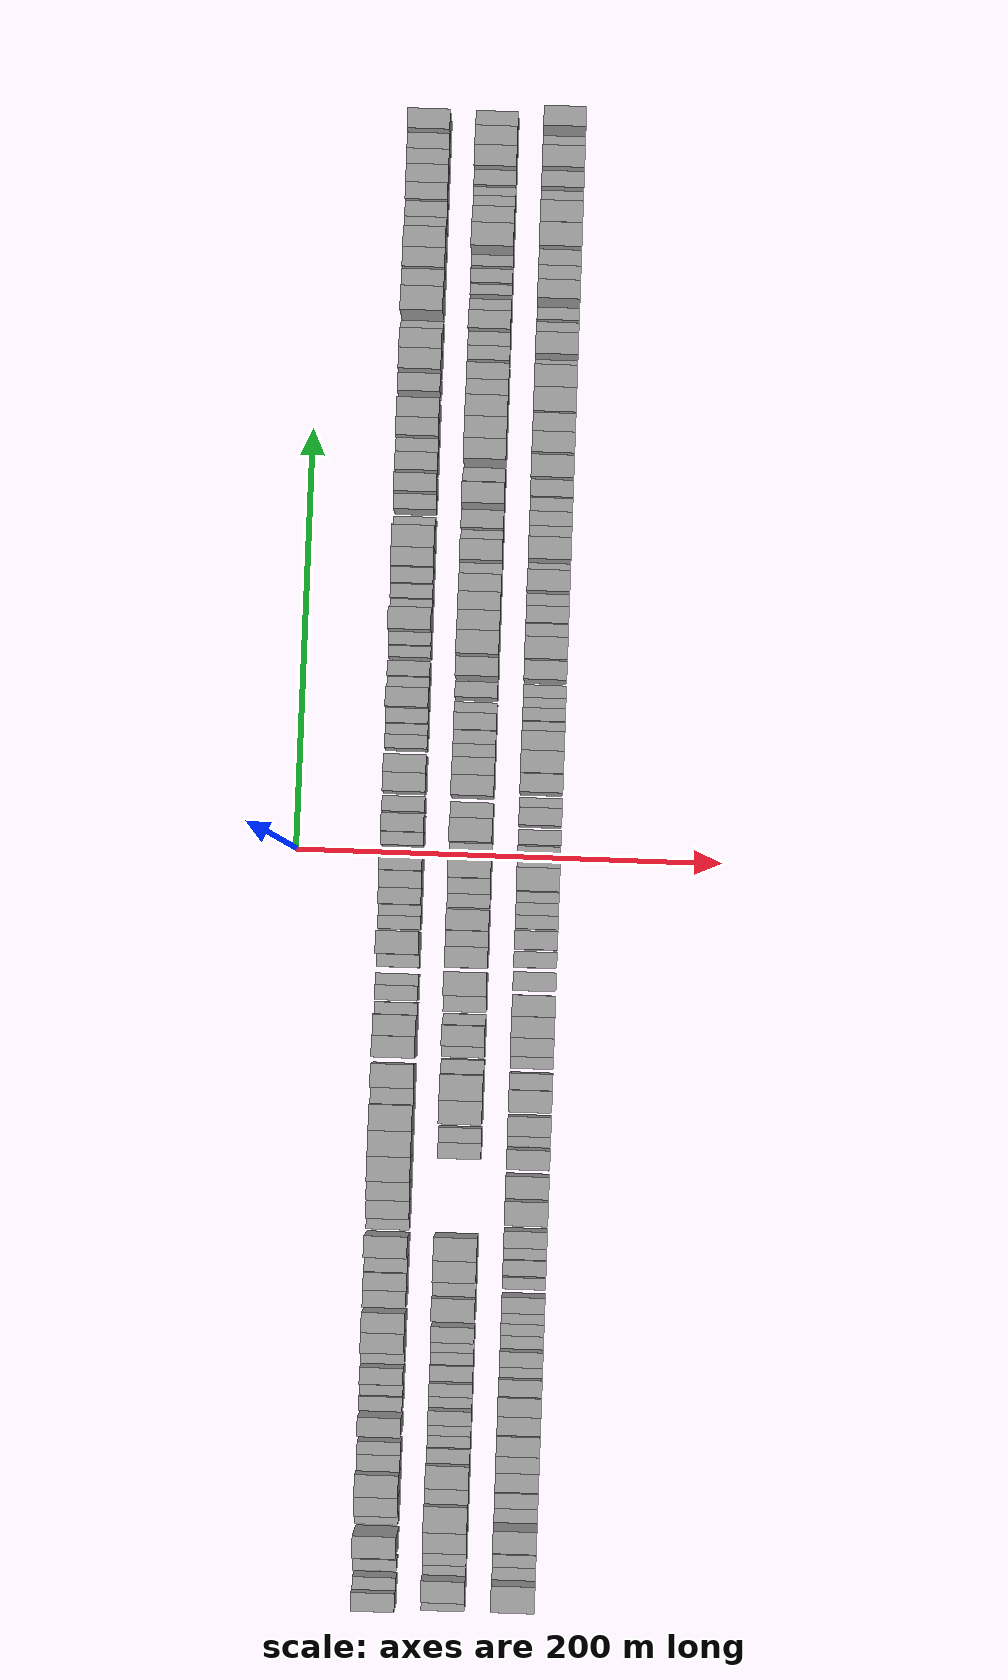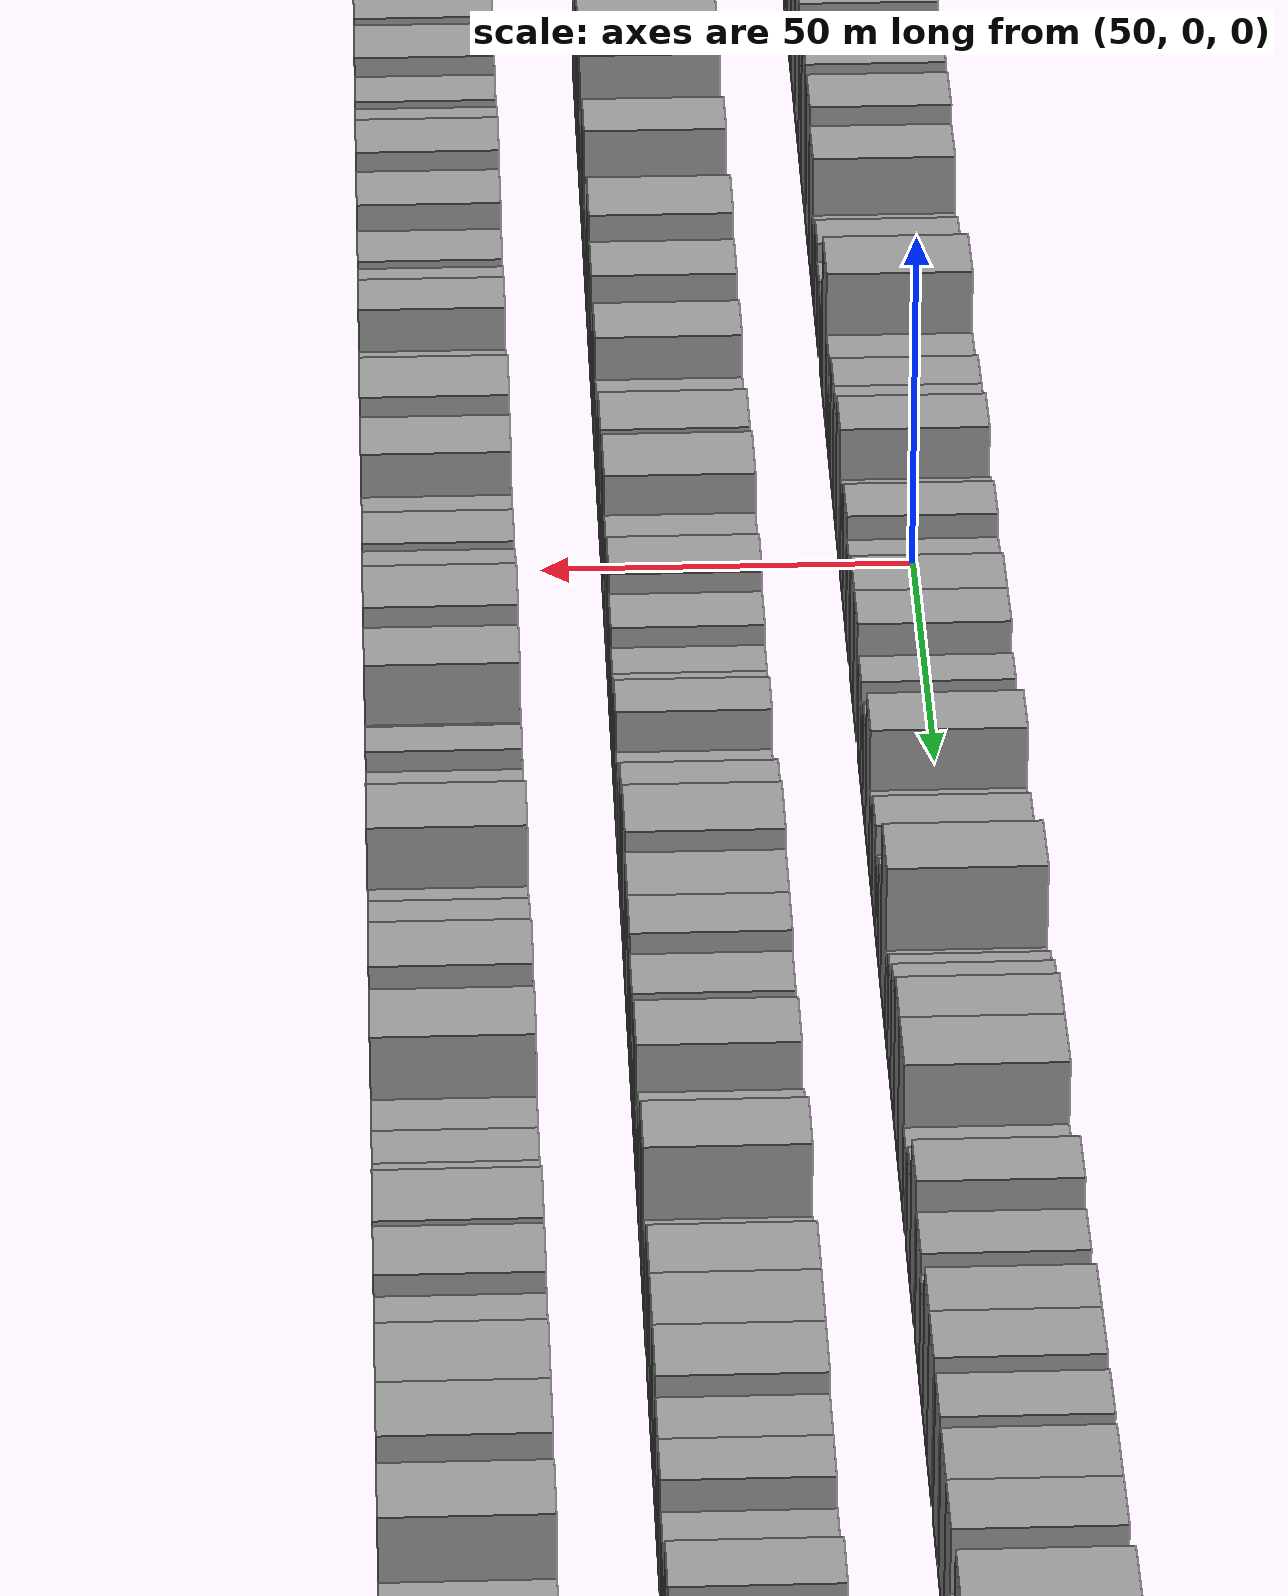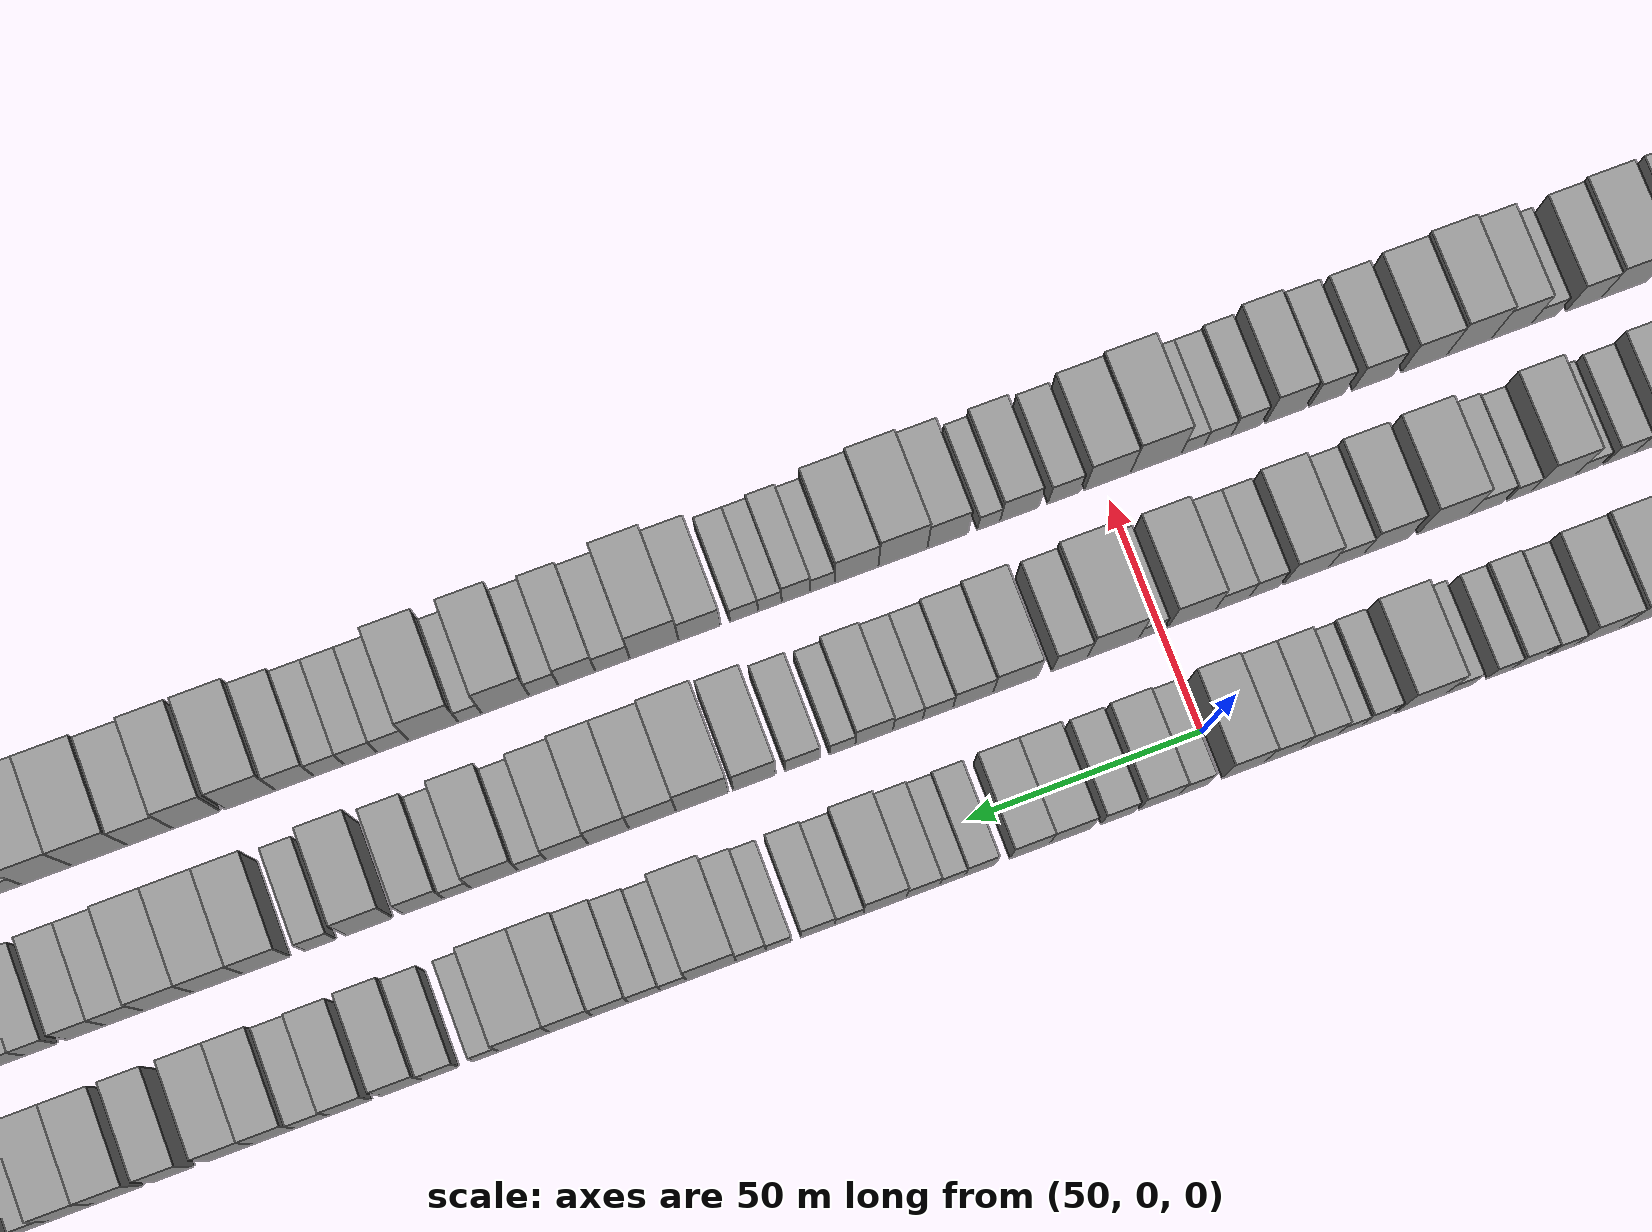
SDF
<sdf version="1.6">
 <world name="default">
  <scene>
   <sky><clouds><speed>12</speed></clouds></sky>
   <ambient>0.4 0.4 0.4 1</ambient>
   <background>0.7 0.7 0.7 1</background>
   <shadows>1</shadows>
  </scene>
  <gravity>0 0 -9.8066</gravity>
  <magnetic_field>6e-06 2.3e-05 -4.2e-05</magnetic_field>
  <physics default="0" name="default_physics" type="ode">
   <ode>
    <solver>
     <type>quick</type>
     <iters>10</iters>
     <sor>1.0</sor>
     <use_dynamic_moi_rescaling>0</use_dynamic_moi_rescaling>
    </solver>
    <constraints>
     <cfm>0</cfm>
     <erp>0.2</erp>
     <contact_max_correcting_vel>100</contact_max_correcting_vel>
     <contact_surface_layer>0.001</contact_surface_layer>
    </constraints>
   </ode>
   <max_step_size>0.004</max_step_size>
   <real_time_factor>1</real_time_factor>
   <real_time_update_rate>250</real_time_update_rate>
  </physics>
  <light name="sun" type="directional">
   <pose>0 0 10 0 0 0</pose>
   <diffuse>0.8 0.8 0.8 1</diffuse>
   <specular>0.2 0.2 0.2 1</specular>
   <attenuation>
    <range>1000</range>
    <constant>0.9</constant>
    <linear>0.01</linear>
    <quadratic>0.001</quadratic>
   </attenuation>
   <direction>-0.5 0.1 -0.9</direction>
  </light>
  <model name="building_1">
   <static>1</static>
   <pose>50.0000 -343.8013 0 0.000000 0.000000 0.000000</pose>
   <link name="link">
    <pose>0 0 9.00 0 0 0</pose>
    <collision name="collision"><geometry><box><size>20.0000 8.3975 18.0000</size></box></geometry></collision>
    <visual name="visual">
     <cast_shadows>0</cast_shadows>
     <geometry><box><size>20.0000 8.3975 18.0000</size></box></geometry>
     <material>
      <script>
       <uri>model://grey_wall/materials/scripts</uri>
       <uri>model://grey_wall/materials/textures</uri>
       <name>vrc/grey_wall</name>
      </script>
     </material>
    </visual>
   </link>
  </model>
  <model name="building_2">
   <static>1</static>
   <pose>50.0000 -336.7153 0 0.000000 0.000000 0.000000</pose>
   <link name="link">
    <pose>0 0 6.00 0 0 0</pose>
    <collision name="collision"><geometry><box><size>20.0000 5.7745 12.0000</size></box></geometry></collision>
    <visual name="visual">
     <cast_shadows>0</cast_shadows>
     <geometry><box><size>20.0000 5.7745 12.0000</size></box></geometry>
     <material>
      <script>
       <uri>model://grey_wall/materials/scripts</uri>
       <uri>model://grey_wall/materials/textures</uri>
       <name>vrc/grey_wall</name>
      </script>
     </material>
    </visual>
   </link>
  </model>
  <model name="building_3">
   <static>1</static>
   <pose>50.0000 -328.2741 0 0.000000 0.000000 0.000000</pose>
   <link name="link">
    <pose>0 0 6.00 0 0 0</pose>
    <collision name="collision"><geometry><box><size>20.0000 5.1080 12.0000</size></box></geometry></collision>
    <visual name="visual">
     <cast_shadows>0</cast_shadows>
     <geometry><box><size>20.0000 5.1080 12.0000</size></box></geometry>
     <material>
      <script>
       <uri>model://grey_wall/materials/scripts</uri>
       <uri>model://grey_wall/materials/textures</uri>
       <name>vrc/grey_wall</name>
      </script>
     </material>
    </visual>
   </link>
  </model>
  <model name="building_4">
   <static>1</static>
   <pose>50.0000 -317.7666 0 0.000000 0.000000 0.000000</pose>
   <link name="link">
    <pose>0 0 12.00 0 0 0</pose>
    <collision name="collision"><geometry><box><size>20.0000 9.9071 24.0000</size></box></geometry></collision>
    <visual name="visual">
     <cast_shadows>0</cast_shadows>
     <geometry><box><size>20.0000 9.9071 24.0000</size></box></geometry>
     <material>
      <script>
       <uri>model://grey_wall/materials/scripts</uri>
       <uri>model://grey_wall/materials/textures</uri>
       <name>vrc/grey_wall</name>
      </script>
     </material>
    </visual>
   </link>
  </model>
  <model name="building_5">
   <static>1</static>
   <pose>50.0000 -307.1703 0 0.000000 0.000000 0.000000</pose>
   <link name="link">
    <pose>0 0 6.00 0 0 0</pose>
    <collision name="collision"><geometry><box><size>20.0000 5.2854 12.0000</size></box></geometry></collision>
    <visual name="visual">
     <cast_shadows>0</cast_shadows>
     <geometry><box><size>20.0000 5.2854 12.0000</size></box></geometry>
     <material>
      <script>
       <uri>model://grey_wall/materials/scripts</uri>
       <uri>model://grey_wall/materials/textures</uri>
       <name>vrc/grey_wall</name>
      </script>
     </material>
    </visual>
   </link>
  </model>
  <model name="building_6">
   <static>1</static>
   <pose>50.0000 -299.9623 0 0.000000 0.000000 0.000000</pose>
   <link name="link">
    <pose>0 0 10.50 0 0 0</pose>
    <collision name="collision"><geometry><box><size>20.0000 9.1305 21.0000</size></box></geometry></collision>
    <visual name="visual">
     <cast_shadows>0</cast_shadows>
     <geometry><box><size>20.0000 9.1305 21.0000</size></box></geometry>
     <material>
      <script>
       <uri>model://grey_wall/materials/scripts</uri>
       <uri>model://grey_wall/materials/textures</uri>
       <name>vrc/grey_wall</name>
      </script>
     </material>
    </visual>
   </link>
  </model>
  <model name="building_7">
   <static>1</static>
   <pose>50.0000 -290.3193 0 0.000000 0.000000 0.000000</pose>
   <link name="link">
    <pose>0 0 12.00 0 0 0</pose>
    <collision name="collision"><geometry><box><size>20.0000 10.1556 24.0000</size></box></geometry></collision>
    <visual name="visual">
     <cast_shadows>0</cast_shadows>
     <geometry><box><size>20.0000 10.1556 24.0000</size></box></geometry>
     <material>
      <script>
       <uri>model://grey_wall/materials/scripts</uri>
       <uri>model://grey_wall/materials/textures</uri>
       <name>vrc/grey_wall</name>
      </script>
     </material>
    </visual>
   </link>
  </model>
  <model name="building_8">
   <static>1</static>
   <pose>50.0000 -281.5235 0 0.000000 0.000000 0.000000</pose>
   <link name="link">
    <pose>0 0 7.50 0 0 0</pose>
    <collision name="collision"><geometry><box><size>20.0000 7.4361 15.0000</size></box></geometry></collision>
    <visual name="visual">
     <cast_shadows>0</cast_shadows>
     <geometry><box><size>20.0000 7.4361 15.0000</size></box></geometry>
     <material>
      <script>
       <uri>model://grey_wall/materials/scripts</uri>
       <uri>model://grey_wall/materials/textures</uri>
       <name>vrc/grey_wall</name>
      </script>
     </material>
    </visual>
   </link>
  </model>
  <model name="building_9">
   <static>1</static>
   <pose>50.0000 -274.7588 0 0.000000 0.000000 0.000000</pose>
   <link name="link">
    <pose>0 0 7.50 0 0 0</pose>
    <collision name="collision"><geometry><box><size>20.0000 6.0932 15.0000</size></box></geometry></collision>
    <visual name="visual">
     <cast_shadows>0</cast_shadows>
     <geometry><box><size>20.0000 6.0932 15.0000</size></box></geometry>
     <material>
      <script>
       <uri>model://grey_wall/materials/scripts</uri>
       <uri>model://grey_wall/materials/textures</uri>
       <name>vrc/grey_wall</name>
      </script>
     </material>
    </visual>
   </link>
  </model>
  <model name="building_10">
   <static>1</static>
   <pose>50.0000 -264.3083 0 0.000000 0.000000 0.000000</pose>
   <link name="link">
    <pose>0 0 10.50 0 0 0</pose>
    <collision name="collision"><geometry><box><size>20.0000 8.8079 21.0000</size></box></geometry></collision>
    <visual name="visual">
     <cast_shadows>0</cast_shadows>
     <geometry><box><size>20.0000 8.8079 21.0000</size></box></geometry>
     <material>
      <script>
       <uri>model://grey_wall/materials/scripts</uri>
       <uri>model://grey_wall/materials/textures</uri>
       <name>vrc/grey_wall</name>
      </script>
     </material>
    </visual>
   </link>
  </model>
  <model name="building_11">
   <static>1</static>
   <pose>50.0000 -254.5786 0 0.000000 0.000000 0.000000</pose>
   <link name="link">
    <pose>0 0 7.50 0 0 0</pose>
    <collision name="collision"><geometry><box><size>20.0000 6.6515 15.0000</size></box></geometry></collision>
    <visual name="visual">
     <cast_shadows>0</cast_shadows>
     <geometry><box><size>20.0000 6.6515 15.0000</size></box></geometry>
     <material>
      <script>
       <uri>model://grey_wall/materials/scripts</uri>
       <uri>model://grey_wall/materials/textures</uri>
       <name>vrc/grey_wall</name>
      </script>
     </material>
    </visual>
   </link>
  </model>
  <model name="building_12">
   <static>1</static>
   <pose>50.0000 -248.8433 0 0.000000 0.000000 0.000000</pose>
   <link name="link">
    <pose>0 0 6.00 0 0 0</pose>
    <collision name="collision"><geometry><box><size>20.0000 4.8192 12.0000</size></box></geometry></collision>
    <visual name="visual">
     <cast_shadows>0</cast_shadows>
     <geometry><box><size>20.0000 4.8192 12.0000</size></box></geometry>
     <material>
      <script>
       <uri>model://grey_wall/materials/scripts</uri>
       <uri>model://grey_wall/materials/textures</uri>
       <name>vrc/grey_wall</name>
      </script>
     </material>
    </visual>
   </link>
  </model>
  <model name="building_13">
   <static>1</static>
   <pose>50.0000 -241.5795 0 0.000000 0.000000 0.000000</pose>
   <link name="link">
    <pose>0 0 9.00 0 0 0</pose>
    <collision name="collision"><geometry><box><size>20.0000 7.7084 18.0000</size></box></geometry></collision>
    <visual name="visual">
     <cast_shadows>0</cast_shadows>
     <geometry><box><size>20.0000 7.7084 18.0000</size></box></geometry>
     <material>
      <script>
       <uri>model://grey_wall/materials/scripts</uri>
       <uri>model://grey_wall/materials/textures</uri>
       <name>vrc/grey_wall</name>
      </script>
     </material>
    </visual>
   </link>
  </model>
  <model name="building_14">
   <static>1</static>
   <pose>50.0000 -233.7702 0 0.000000 0.000000 0.000000</pose>
   <link name="link">
    <pose>0 0 6.00 0 0 0</pose>
    <collision name="collision"><geometry><box><size>20.0000 5.9101 12.0000</size></box></geometry></collision>
    <visual name="visual">
     <cast_shadows>0</cast_shadows>
     <geometry><box><size>20.0000 5.9101 12.0000</size></box></geometry>
     <material>
      <script>
       <uri>model://grey_wall/materials/scripts</uri>
       <uri>model://grey_wall/materials/textures</uri>
       <name>vrc/grey_wall</name>
      </script>
     </material>
    </visual>
   </link>
  </model>
  <model name="building_15">
   <static>1</static>
   <pose>50.0000 -226.2153 0 0.000000 0.000000 0.000000</pose>
   <link name="link">
    <pose>0 0 10.50 0 0 0</pose>
    <collision name="collision"><geometry><box><size>20.0000 9.1998 21.0000</size></box></geometry></collision>
    <visual name="visual">
     <cast_shadows>0</cast_shadows>
     <geometry><box><size>20.0000 9.1998 21.0000</size></box></geometry>
     <material>
      <script>
       <uri>model://grey_wall/materials/scripts</uri>
       <uri>model://grey_wall/materials/textures</uri>
       <name>vrc/grey_wall</name>
      </script>
     </material>
    </visual>
   </link>
  </model>
  <model name="building_16">
   <static>1</static>
   <pose>50.0000 -216.9937 0 0.000000 0.000000 0.000000</pose>
   <link name="link">
    <pose>0 0 10.50 0 0 0</pose>
    <collision name="collision"><geometry><box><size>20.0000 9.2434 21.0000</size></box></geometry></collision>
    <visual name="visual">
     <cast_shadows>0</cast_shadows>
     <geometry><box><size>20.0000 9.2434 21.0000</size></box></geometry>
     <material>
      <script>
       <uri>model://grey_wall/materials/scripts</uri>
       <uri>model://grey_wall/materials/textures</uri>
       <name>vrc/grey_wall</name>
      </script>
     </material>
    </visual>
   </link>
  </model>
  <model name="building_17">
   <static>1</static>
   <pose>50.0000 -206.4832 0 0.000000 0.000000 0.000000</pose>
   <link name="link">
    <pose>0 0 9.00 0 0 0</pose>
    <collision name="collision"><geometry><box><size>20.0000 7.7774 18.0000</size></box></geometry></collision>
    <visual name="visual">
     <cast_shadows>0</cast_shadows>
     <geometry><box><size>20.0000 7.7774 18.0000</size></box></geometry>
     <material>
      <script>
       <uri>model://grey_wall/materials/scripts</uri>
       <uri>model://grey_wall/materials/textures</uri>
       <name>vrc/grey_wall</name>
      </script>
     </material>
    </visual>
   </link>
  </model>
  <model name="building_18">
   <static>1</static>
   <pose>50.0000 -198.5400 0 0.000000 0.000000 0.000000</pose>
   <link name="link">
    <pose>0 0 9.00 0 0 0</pose>
    <collision name="collision"><geometry><box><size>20.0000 8.1091 18.0000</size></box></geometry></collision>
    <visual name="visual">
     <cast_shadows>0</cast_shadows>
     <geometry><box><size>20.0000 8.1091 18.0000</size></box></geometry>
     <material>
      <script>
       <uri>model://grey_wall/materials/scripts</uri>
       <uri>model://grey_wall/materials/textures</uri>
       <name>vrc/grey_wall</name>
      </script>
     </material>
    </visual>
   </link>
  </model>
  <model name="building_19">
   <static>1</static>
   <pose>50.0000 -190.7908 0 0.000000 0.000000 0.000000</pose>
   <link name="link">
    <pose>0 0 7.50 0 0 0</pose>
    <collision name="collision"><geometry><box><size>20.0000 7.3893 15.0000</size></box></geometry></collision>
    <visual name="visual">
     <cast_shadows>0</cast_shadows>
     <geometry><box><size>20.0000 7.3893 15.0000</size></box></geometry>
     <material>
      <script>
       <uri>model://grey_wall/materials/scripts</uri>
       <uri>model://grey_wall/materials/textures</uri>
       <name>vrc/grey_wall</name>
      </script>
     </material>
    </visual>
   </link>
  </model>
  <model name="building_20">
   <static>1</static>
   <pose>50.0000 -182.1305 0 0.000000 0.000000 0.000000</pose>
   <link name="link">
    <pose>0 0 12.00 0 0 0</pose>
    <collision name="collision"><geometry><box><size>20.0000 9.9312 24.0000</size></box></geometry></collision>
    <visual name="visual">
     <cast_shadows>0</cast_shadows>
     <geometry><box><size>20.0000 9.9312 24.0000</size></box></geometry>
     <material>
      <script>
       <uri>model://grey_wall/materials/scripts</uri>
       <uri>model://grey_wall/materials/textures</uri>
       <name>vrc/grey_wall</name>
      </script>
     </material>
    </visual>
   </link>
  </model>
  <model name="building_21">
   <static>1</static>
   <pose>50.0000 -172.4947 0 0.000000 0.000000 0.000000</pose>
   <link name="link">
    <pose>0 0 6.00 0 0 0</pose>
    <collision name="collision"><geometry><box><size>20.0000 5.3402 12.0000</size></box></geometry></collision>
    <visual name="visual">
     <cast_shadows>0</cast_shadows>
     <geometry><box><size>20.0000 5.3402 12.0000</size></box></geometry>
     <material>
      <script>
       <uri>model://grey_wall/materials/scripts</uri>
       <uri>model://grey_wall/materials/textures</uri>
       <name>vrc/grey_wall</name>
      </script>
     </material>
    </visual>
   </link>
  </model>
  <model name="building_22">
   <static>1</static>
   <pose>50.0000 -165.4881 0 0.000000 0.000000 0.000000</pose>
   <link name="link">
    <pose>0 0 9.00 0 0 0</pose>
    <collision name="collision"><geometry><box><size>20.0000 8.6730 18.0000</size></box></geometry></collision>
    <visual name="visual">
     <cast_shadows>0</cast_shadows>
     <geometry><box><size>20.0000 8.6730 18.0000</size></box></geometry>
     <material>
      <script>
       <uri>model://grey_wall/materials/scripts</uri>
       <uri>model://grey_wall/materials/textures</uri>
       <name>vrc/grey_wall</name>
      </script>
     </material>
    </visual>
   </link>
  </model>
  <model name="building_23">
   <static>1</static>
   <pose>50.0000 -156.8079 0 0.000000 0.000000 0.000000</pose>
   <link name="link">
    <pose>0 0 10.50 0 0 0</pose>
    <collision name="collision"><geometry><box><size>20.0000 8.6874 21.0000</size></box></geometry></collision>
    <visual name="visual">
     <cast_shadows>0</cast_shadows>
     <geometry><box><size>20.0000 8.6874 21.0000</size></box></geometry>
     <material>
      <script>
       <uri>model://grey_wall/materials/scripts</uri>
       <uri>model://grey_wall/materials/textures</uri>
       <name>vrc/grey_wall</name>
      </script>
     </material>
    </visual>
   </link>
  </model>
  <model name="building_24">
   <static>1</static>
   <pose>50.0000 -146.7155 0 0.000000 0.000000 0.000000</pose>
   <link name="link">
    <pose>0 0 12.00 0 0 0</pose>
    <collision name="collision"><geometry><box><size>20.0000 11.4976 24.0000</size></box></geometry></collision>
    <visual name="visual">
     <cast_shadows>0</cast_shadows>
     <geometry><box><size>20.0000 11.4976 24.0000</size></box></geometry>
     <material>
      <script>
       <uri>model://grey_wall/materials/scripts</uri>
       <uri>model://grey_wall/materials/textures</uri>
       <name>vrc/grey_wall</name>
      </script>
     </material>
    </visual>
   </link>
  </model>
  <model name="building_25">
   <static>1</static>
   <pose>50.0000 -135.0739 0 0.000000 0.000000 0.000000</pose>
   <link name="link">
    <pose>0 0 12.00 0 0 0</pose>
    <collision name="collision"><geometry><box><size>20.0000 11.7856 24.0000</size></box></geometry></collision>
    <visual name="visual">
     <cast_shadows>0</cast_shadows>
     <geometry><box><size>20.0000 11.7856 24.0000</size></box></geometry>
     <material>
      <script>
       <uri>model://grey_wall/materials/scripts</uri>
       <uri>model://grey_wall/materials/textures</uri>
       <name>vrc/grey_wall</name>
      </script>
     </material>
    </visual>
   </link>
  </model>
  <model name="building_26">
   <static>1</static>
   <pose>50.0000 -123.1845 0 0.000000 0.000000 0.000000</pose>
   <link name="link">
    <pose>0 0 12.00 0 0 0</pose>
    <collision name="collision"><geometry><box><size>20.0000 11.9932 24.0000</size></box></geometry></collision>
    <visual name="visual">
     <cast_shadows>0</cast_shadows>
     <geometry><box><size>20.0000 11.9932 24.0000</size></box></geometry>
     <material>
      <script>
       <uri>model://grey_wall/materials/scripts</uri>
       <uri>model://grey_wall/materials/textures</uri>
       <name>vrc/grey_wall</name>
      </script>
     </material>
    </visual>
   </link>
  </model>
  <model name="building_27">
   <static>1</static>
   <pose>50.0000 -113.3230 0 0.000000 0.000000 0.000000</pose>
   <link name="link">
    <pose>0 0 9.00 0 0 0</pose>
    <collision name="collision"><geometry><box><size>20.0000 7.7298 18.0000</size></box></geometry></collision>
    <visual name="visual">
     <cast_shadows>0</cast_shadows>
     <geometry><box><size>20.0000 7.7298 18.0000</size></box></geometry>
     <material>
      <script>
       <uri>model://grey_wall/materials/scripts</uri>
       <uri>model://grey_wall/materials/textures</uri>
       <name>vrc/grey_wall</name>
      </script>
     </material>
    </visual>
   </link>
  </model>
  <model name="building_28">
   <static>1</static>
   <pose>50.0000 -104.0030 0 0.000000 0.000000 0.000000</pose>
   <link name="link">
    <pose>0 0 12.00 0 0 0</pose>
    <collision name="collision"><geometry><box><size>20.0000 10.9103 24.0000</size></box></geometry></collision>
    <visual name="visual">
     <cast_shadows>0</cast_shadows>
     <geometry><box><size>20.0000 10.9103 24.0000</size></box></geometry>
     <material>
      <script>
       <uri>model://grey_wall/materials/scripts</uri>
       <uri>model://grey_wall/materials/textures</uri>
       <name>vrc/grey_wall</name>
      </script>
     </material>
    </visual>
   </link>
  </model>
  <model name="building_29">
   <static>1</static>
   <pose>50.0000 -90.6180 0 0.000000 0.000000 0.000000</pose>
   <link name="link">
    <pose>0 0 12.00 0 0 0</pose>
    <collision name="collision"><geometry><box><size>20.0000 9.8597 24.0000</size></box></geometry></collision>
    <visual name="visual">
     <cast_shadows>0</cast_shadows>
     <geometry><box><size>20.0000 9.8597 24.0000</size></box></geometry>
     <material>
      <script>
       <uri>model://grey_wall/materials/scripts</uri>
       <uri>model://grey_wall/materials/textures</uri>
       <name>vrc/grey_wall</name>
      </script>
     </material>
    </visual>
   </link>
  </model>
  <model name="building_30">
   <static>1</static>
   <pose>50.0000 -80.7948 0 0.000000 0.000000 0.000000</pose>
   <link name="link">
    <pose>0 0 10.50 0 0 0</pose>
    <collision name="collision"><geometry><box><size>20.0000 9.7866 21.0000</size></box></geometry></collision>
    <visual name="visual">
     <cast_shadows>0</cast_shadows>
     <geometry><box><size>20.0000 9.7866 21.0000</size></box></geometry>
     <material>
      <script>
       <uri>model://grey_wall/materials/scripts</uri>
       <uri>model://grey_wall/materials/textures</uri>
       <name>vrc/grey_wall</name>
      </script>
     </material>
    </visual>
   </link>
  </model>
  <model name="building_31">
   <static>1</static>
   <pose>50.0000 -73.0840 0 0.000000 0.000000 0.000000</pose>
   <link name="link">
    <pose>0 0 6.00 0 0 0</pose>
    <collision name="collision"><geometry><box><size>20.0000 5.6350 12.0000</size></box></geometry></collision>
    <visual name="visual">
     <cast_shadows>0</cast_shadows>
     <geometry><box><size>20.0000 5.6350 12.0000</size></box></geometry>
     <material>
      <script>
       <uri>model://grey_wall/materials/scripts</uri>
       <uri>model://grey_wall/materials/textures</uri>
       <name>vrc/grey_wall</name>
      </script>
     </material>
    </visual>
   </link>
  </model>
  <model name="building_32">
   <static>1</static>
   <pose>50.0000 -65.8188 0 0.000000 0.000000 0.000000</pose>
   <link name="link">
    <pose>0 0 7.50 0 0 0</pose>
    <collision name="collision"><geometry><box><size>20.0000 6.8953 15.0000</size></box></geometry></collision>
    <visual name="visual">
     <cast_shadows>0</cast_shadows>
     <geometry><box><size>20.0000 6.8953 15.0000</size></box></geometry>
     <material>
      <script>
       <uri>model://grey_wall/materials/scripts</uri>
       <uri>model://grey_wall/materials/textures</uri>
       <name>vrc/grey_wall</name>
      </script>
     </material>
    </visual>
   </link>
  </model>
  <model name="building_33">
   <static>1</static>
   <pose>50.0000 -59.6312 0 0.000000 0.000000 0.000000</pose>
   <link name="link">
    <pose>0 0 6.00 0 0 0</pose>
    <collision name="collision"><geometry><box><size>20.0000 5.4799 12.0000</size></box></geometry></collision>
    <visual name="visual">
     <cast_shadows>0</cast_shadows>
     <geometry><box><size>20.0000 5.4799 12.0000</size></box></geometry>
     <material>
      <script>
       <uri>model://grey_wall/materials/scripts</uri>
       <uri>model://grey_wall/materials/textures</uri>
       <name>vrc/grey_wall</name>
      </script>
     </material>
    </visual>
   </link>
  </model>
  <model name="building_34">
   <static>1</static>
   <pose>50.0000 -50.9362 0 0.000000 0.000000 0.000000</pose>
   <link name="link">
    <pose>0 0 6.00 0 0 0</pose>
    <collision name="collision"><geometry><box><size>20.0000 5.9099 12.0000</size></box></geometry></collision>
    <visual name="visual">
     <cast_shadows>0</cast_shadows>
     <geometry><box><size>20.0000 5.9099 12.0000</size></box></geometry>
     <material>
      <script>
       <uri>model://grey_wall/materials/scripts</uri>
       <uri>model://grey_wall/materials/textures</uri>
       <name>vrc/grey_wall</name>
      </script>
     </material>
    </visual>
   </link>
  </model>
  <model name="building_35">
   <static>1</static>
   <pose>50.0000 -42.6697 0 0.000000 0.000000 0.000000</pose>
   <link name="link">
    <pose>0 0 12.00 0 0 0</pose>
    <collision name="collision"><geometry><box><size>20.0000 10.6231 24.0000</size></box></geometry></collision>
    <visual name="visual">
     <cast_shadows>0</cast_shadows>
     <geometry><box><size>20.0000 10.6231 24.0000</size></box></geometry>
     <material>
      <script>
       <uri>model://grey_wall/materials/scripts</uri>
       <uri>model://grey_wall/materials/textures</uri>
       <name>vrc/grey_wall</name>
      </script>
     </material>
    </visual>
   </link>
  </model>
  <model name="building_36">
   <static>1</static>
   <pose>50.0000 -33.2216 0 0.000000 0.000000 0.000000</pose>
   <link name="link">
    <pose>0 0 7.50 0 0 0</pose>
    <collision name="collision"><geometry><box><size>20.0000 6.2732 15.0000</size></box></geometry></collision>
    <visual name="visual">
     <cast_shadows>0</cast_shadows>
     <geometry><box><size>20.0000 6.2732 15.0000</size></box></geometry>
     <material>
      <script>
       <uri>model://grey_wall/materials/scripts</uri>
       <uri>model://grey_wall/materials/textures</uri>
       <name>vrc/grey_wall</name>
      </script>
     </material>
    </visual>
   </link>
  </model>
  <model name="building_37">
   <static>1</static>
   <pose>50.0000 -27.4517 0 0.000000 0.000000 0.000000</pose>
   <link name="link">
    <pose>0 0 6.00 0 0 0</pose>
    <collision name="collision"><geometry><box><size>20.0000 5.2666 12.0000</size></box></geometry></collision>
    <visual name="visual">
     <cast_shadows>0</cast_shadows>
     <geometry><box><size>20.0000 5.2666 12.0000</size></box></geometry>
     <material>
      <script>
       <uri>model://grey_wall/materials/scripts</uri>
       <uri>model://grey_wall/materials/textures</uri>
       <name>vrc/grey_wall</name>
      </script>
     </material>
    </visual>
   </link>
  </model>
  <model name="building_38">
   <static>1</static>
   <pose>50.0000 -20.9841 0 0.000000 0.000000 0.000000</pose>
   <link name="link">
    <pose>0 0 9.00 0 0 0</pose>
    <collision name="collision"><geometry><box><size>20.0000 7.6684 18.0000</size></box></geometry></collision>
    <visual name="visual">
     <cast_shadows>0</cast_shadows>
     <geometry><box><size>20.0000 7.6684 18.0000</size></box></geometry>
     <material>
      <script>
       <uri>model://grey_wall/materials/scripts</uri>
       <uri>model://grey_wall/materials/textures</uri>
       <name>vrc/grey_wall</name>
      </script>
     </material>
    </visual>
   </link>
  </model>
  <model name="building_39">
   <static>1</static>
   <pose>50.0000 -13.1733 0 0.000000 0.000000 0.000000</pose>
   <link name="link">
    <pose>0 0 9.00 0 0 0</pose>
    <collision name="collision"><geometry><box><size>20.0000 7.9532 18.0000</size></box></geometry></collision>
    <visual name="visual">
     <cast_shadows>0</cast_shadows>
     <geometry><box><size>20.0000 7.9532 18.0000</size></box></geometry>
     <material>
      <script>
       <uri>model://grey_wall/materials/scripts</uri>
       <uri>model://grey_wall/materials/textures</uri>
       <name>vrc/grey_wall</name>
      </script>
     </material>
    </visual>
   </link>
  </model>
  <model name="building_40">
   <static>1</static>
   <pose>50.0000 -4.7007 0 0.000000 0.000000 0.000000</pose>
   <link name="link">
    <pose>0 0 10.50 0 0 0</pose>
    <collision name="collision"><geometry><box><size>20.0000 8.9920 21.0000</size></box></geometry></collision>
    <visual name="visual">
     <cast_shadows>0</cast_shadows>
     <geometry><box><size>20.0000 8.9920 21.0000</size></box></geometry>
     <material>
      <script>
       <uri>model://grey_wall/materials/scripts</uri>
       <uri>model://grey_wall/materials/textures</uri>
       <name>vrc/grey_wall</name>
      </script>
     </material>
    </visual>
   </link>
  </model>
  <model name="building_41">
   <static>1</static>
   <pose>50.0000 5.8593 0 0.000000 0.000000 0.000000</pose>
   <link name="link">
    <pose>0 0 7.50 0 0 0</pose>
    <collision name="collision"><geometry><box><size>20.0000 6.1280 15.0000</size></box></geometry></collision>
    <visual name="visual">
     <cast_shadows>0</cast_shadows>
     <geometry><box><size>20.0000 6.1280 15.0000</size></box></geometry>
     <material>
      <script>
       <uri>model://grey_wall/materials/scripts</uri>
       <uri>model://grey_wall/materials/textures</uri>
       <name>vrc/grey_wall</name>
      </script>
     </material>
    </visual>
   </link>
  </model>
  <model name="building_42">
   <static>1</static>
   <pose>50.0000 13.2089 0 0.000000 0.000000 0.000000</pose>
   <link name="link">
    <pose>0 0 9.00 0 0 0</pose>
    <collision name="collision"><geometry><box><size>20.0000 8.5713 18.0000</size></box></geometry></collision>
    <visual name="visual">
     <cast_shadows>0</cast_shadows>
     <geometry><box><size>20.0000 8.5713 18.0000</size></box></geometry>
     <material>
      <script>
       <uri>model://grey_wall/materials/scripts</uri>
       <uri>model://grey_wall/materials/textures</uri>
       <name>vrc/grey_wall</name>
      </script>
     </material>
    </visual>
   </link>
  </model>
  <model name="building_43">
   <static>1</static>
   <pose>50.0000 22.0549 0 0.000000 0.000000 0.000000</pose>
   <link name="link">
    <pose>0 0 7.50 0 0 0</pose>
    <collision name="collision"><geometry><box><size>20.0000 7.1205 15.0000</size></box></geometry></collision>
    <visual name="visual">
     <cast_shadows>0</cast_shadows>
     <geometry><box><size>20.0000 7.1205 15.0000</size></box></geometry>
     <material>
      <script>
       <uri>model://grey_wall/materials/scripts</uri>
       <uri>model://grey_wall/materials/textures</uri>
       <name>vrc/grey_wall</name>
      </script>
     </material>
    </visual>
   </link>
  </model>
  <model name="building_44">
   <static>1</static>
   <pose>50.0000 32.0292 0 0.000000 0.000000 0.000000</pose>
   <link name="link">
    <pose>0 0 9.00 0 0 0</pose>
    <collision name="collision"><geometry><box><size>20.0000 8.8283 18.0000</size></box></geometry></collision>
    <visual name="visual">
     <cast_shadows>0</cast_shadows>
     <geometry><box><size>20.0000 8.8283 18.0000</size></box></geometry>
     <material>
      <script>
       <uri>model://grey_wall/materials/scripts</uri>
       <uri>model://grey_wall/materials/textures</uri>
       <name>vrc/grey_wall</name>
      </script>
     </material>
    </visual>
   </link>
  </model>
  <model name="building_45">
   <static>1</static>
   <pose>50.0000 40.6989 0 0.000000 0.000000 0.000000</pose>
   <link name="link">
    <pose>0 0 9.00 0 0 0</pose>
    <collision name="collision"><geometry><box><size>20.0000 8.5111 18.0000</size></box></geometry></collision>
    <visual name="visual">
     <cast_shadows>0</cast_shadows>
     <geometry><box><size>20.0000 8.5111 18.0000</size></box></geometry>
     <material>
      <script>
       <uri>model://grey_wall/materials/scripts</uri>
       <uri>model://grey_wall/materials/textures</uri>
       <name>vrc/grey_wall</name>
      </script>
     </material>
    </visual>
   </link>
  </model>
  <model name="building_46">
   <static>1</static>
   <pose>50.0000 51.1816 0 0.000000 0.000000 0.000000</pose>
   <link name="link">
    <pose>0 0 7.50 0 0 0</pose>
    <collision name="collision"><geometry><box><size>20.0000 6.4541 15.0000</size></box></geometry></collision>
    <visual name="visual">
     <cast_shadows>0</cast_shadows>
     <geometry><box><size>20.0000 6.4541 15.0000</size></box></geometry>
     <material>
      <script>
       <uri>model://grey_wall/materials/scripts</uri>
       <uri>model://grey_wall/materials/textures</uri>
       <name>vrc/grey_wall</name>
      </script>
     </material>
    </visual>
   </link>
  </model>
  <model name="building_47">
   <static>1</static>
   <pose>50.0000 57.1054 0 0.000000 0.000000 0.000000</pose>
   <link name="link">
    <pose>0 0 6.00 0 0 0</pose>
    <collision name="collision"><geometry><box><size>20.0000 5.3936 12.0000</size></box></geometry></collision>
    <visual name="visual">
     <cast_shadows>0</cast_shadows>
     <geometry><box><size>20.0000 5.3936 12.0000</size></box></geometry>
     <material>
      <script>
       <uri>model://grey_wall/materials/scripts</uri>
       <uri>model://grey_wall/materials/textures</uri>
       <name>vrc/grey_wall</name>
      </script>
     </material>
    </visual>
   </link>
  </model>
  <model name="building_48">
   <static>1</static>
   <pose>50.0000 63.3091 0 0.000000 0.000000 0.000000</pose>
   <link name="link">
    <pose>0 0 7.50 0 0 0</pose>
    <collision name="collision"><geometry><box><size>20.0000 7.0137 15.0000</size></box></geometry></collision>
    <visual name="visual">
     <cast_shadows>0</cast_shadows>
     <geometry><box><size>20.0000 7.0137 15.0000</size></box></geometry>
     <material>
      <script>
       <uri>model://grey_wall/materials/scripts</uri>
       <uri>model://grey_wall/materials/textures</uri>
       <name>vrc/grey_wall</name>
      </script>
     </material>
    </visual>
   </link>
  </model>
  <model name="building_49">
   <static>1</static>
   <pose>50.0000 71.3637 0 0.000000 0.000000 0.000000</pose>
   <link name="link">
    <pose>0 0 10.50 0 0 0</pose>
    <collision name="collision"><geometry><box><size>20.0000 9.0956 21.0000</size></box></geometry></collision>
    <visual name="visual">
     <cast_shadows>0</cast_shadows>
     <geometry><box><size>20.0000 9.0956 21.0000</size></box></geometry>
     <material>
      <script>
       <uri>model://grey_wall/materials/scripts</uri>
       <uri>model://grey_wall/materials/textures</uri>
       <name>vrc/grey_wall</name>
      </script>
     </material>
    </visual>
   </link>
  </model>
  <model name="building_50">
   <static>1</static>
   <pose>50.0000 78.8789 0 0.000000 0.000000 0.000000</pose>
   <link name="link">
    <pose>0 0 6.00 0 0 0</pose>
    <collision name="collision"><geometry><box><size>20.0000 5.9347 12.0000</size></box></geometry></collision>
    <visual name="visual">
     <cast_shadows>0</cast_shadows>
     <geometry><box><size>20.0000 5.9347 12.0000</size></box></geometry>
     <material>
      <script>
       <uri>model://grey_wall/materials/scripts</uri>
       <uri>model://grey_wall/materials/textures</uri>
       <name>vrc/grey_wall</name>
      </script>
     </material>
    </visual>
   </link>
  </model>
  <model name="building_51">
   <static>1</static>
   <pose>50.0000 85.4287 0 0.000000 0.000000 0.000000</pose>
   <link name="link">
    <pose>0 0 7.50 0 0 0</pose>
    <collision name="collision"><geometry><box><size>20.0000 7.1651 15.0000</size></box></geometry></collision>
    <visual name="visual">
     <cast_shadows>0</cast_shadows>
     <geometry><box><size>20.0000 7.1651 15.0000</size></box></geometry>
     <material>
      <script>
       <uri>model://grey_wall/materials/scripts</uri>
       <uri>model://grey_wall/materials/textures</uri>
       <name>vrc/grey_wall</name>
      </script>
     </material>
    </visual>
   </link>
  </model>
  <model name="building_52">
   <static>1</static>
   <pose>50.0000 93.6907 0 0.000000 0.000000 0.000000</pose>
   <link name="link">
    <pose>0 0 6.00 0 0 0</pose>
    <collision name="collision"><geometry><box><size>20.0000 5.3589 12.0000</size></box></geometry></collision>
    <visual name="visual">
     <cast_shadows>0</cast_shadows>
     <geometry><box><size>20.0000 5.3589 12.0000</size></box></geometry>
     <material>
      <script>
       <uri>model://grey_wall/materials/scripts</uri>
       <uri>model://grey_wall/materials/textures</uri>
       <name>vrc/grey_wall</name>
      </script>
     </material>
    </visual>
   </link>
  </model>
  <model name="building_53">
   <static>1</static>
   <pose>50.0000 99.4833 0 0.000000 0.000000 0.000000</pose>
   <link name="link">
    <pose>0 0 7.50 0 0 0</pose>
    <collision name="collision"><geometry><box><size>20.0000 6.2262 15.0000</size></box></geometry></collision>
    <visual name="visual">
     <cast_shadows>0</cast_shadows>
     <geometry><box><size>20.0000 6.2262 15.0000</size></box></geometry>
     <material>
      <script>
       <uri>model://grey_wall/materials/scripts</uri>
       <uri>model://grey_wall/materials/textures</uri>
       <name>vrc/grey_wall</name>
      </script>
     </material>
    </visual>
   </link>
  </model>
  <model name="building_54">
   <static>1</static>
   <pose>50.0000 107.8251 0 0.000000 0.000000 0.000000</pose>
   <link name="link">
    <pose>0 0 12.00 0 0 0</pose>
    <collision name="collision"><geometry><box><size>20.0000 10.4574 24.0000</size></box></geometry></collision>
    <visual name="visual">
     <cast_shadows>0</cast_shadows>
     <geometry><box><size>20.0000 10.4574 24.0000</size></box></geometry>
     <material>
      <script>
       <uri>model://grey_wall/materials/scripts</uri>
       <uri>model://grey_wall/materials/textures</uri>
       <name>vrc/grey_wall</name>
      </script>
     </material>
    </visual>
   </link>
  </model>
  <model name="building_55">
   <static>1</static>
   <pose>50.0000 115.7658 0 0.000000 0.000000 0.000000</pose>
   <link name="link">
    <pose>0 0 6.00 0 0 0</pose>
    <collision name="collision"><geometry><box><size>20.0000 5.4240 12.0000</size></box></geometry></collision>
    <visual name="visual">
     <cast_shadows>0</cast_shadows>
     <geometry><box><size>20.0000 5.4240 12.0000</size></box></geometry>
     <material>
      <script>
       <uri>model://grey_wall/materials/scripts</uri>
       <uri>model://grey_wall/materials/textures</uri>
       <name>vrc/grey_wall</name>
      </script>
     </material>
    </visual>
   </link>
  </model>
  <model name="building_56">
   <static>1</static>
   <pose>50.0000 121.8006 0 0.000000 0.000000 0.000000</pose>
   <link name="link">
    <pose>0 0 7.50 0 0 0</pose>
    <collision name="collision"><geometry><box><size>20.0000 6.6455 15.0000</size></box></geometry></collision>
    <visual name="visual">
     <cast_shadows>0</cast_shadows>
     <geometry><box><size>20.0000 6.6455 15.0000</size></box></geometry>
     <material>
      <script>
       <uri>model://grey_wall/materials/scripts</uri>
       <uri>model://grey_wall/materials/textures</uri>
       <name>vrc/grey_wall</name>
      </script>
     </material>
    </visual>
   </link>
  </model>
  <model name="building_57">
   <static>1</static>
   <pose>50.0000 128.8686 0 0.000000 0.000000 0.000000</pose>
   <link name="link">
    <pose>0 0 9.00 0 0 0</pose>
    <collision name="collision"><geometry><box><size>20.0000 7.4904 18.0000</size></box></geometry></collision>
    <visual name="visual">
     <cast_shadows>0</cast_shadows>
     <geometry><box><size>20.0000 7.4904 18.0000</size></box></geometry>
     <material>
      <script>
       <uri>model://grey_wall/materials/scripts</uri>
       <uri>model://grey_wall/materials/textures</uri>
       <name>vrc/grey_wall</name>
      </script>
     </material>
    </visual>
   </link>
  </model>
  <model name="building_58">
   <static>1</static>
   <pose>50.0000 137.0572 0 0.000000 0.000000 0.000000</pose>
   <link name="link">
    <pose>0 0 10.50 0 0 0</pose>
    <collision name="collision"><geometry><box><size>20.0000 8.8868 21.0000</size></box></geometry></collision>
    <visual name="visual">
     <cast_shadows>0</cast_shadows>
     <geometry><box><size>20.0000 8.8868 21.0000</size></box></geometry>
     <material>
      <script>
       <uri>model://grey_wall/materials/scripts</uri>
       <uri>model://grey_wall/materials/textures</uri>
       <name>vrc/grey_wall</name>
      </script>
     </material>
    </visual>
   </link>
  </model>
  <model name="building_59">
   <static>1</static>
   <pose>50.0000 146.7408 0 0.000000 0.000000 0.000000</pose>
   <link name="link">
    <pose>0 0 10.50 0 0 0</pose>
    <collision name="collision"><geometry><box><size>20.0000 10.4805 21.0000</size></box></geometry></collision>
    <visual name="visual">
     <cast_shadows>0</cast_shadows>
     <geometry><box><size>20.0000 10.4805 21.0000</size></box></geometry>
     <material>
      <script>
       <uri>model://grey_wall/materials/scripts</uri>
       <uri>model://grey_wall/materials/textures</uri>
       <name>vrc/grey_wall</name>
      </script>
     </material>
    </visual>
   </link>
  </model>
  <model name="building_60">
   <static>1</static>
   <pose>50.0000 154.7017 0 0.000000 0.000000 0.000000</pose>
   <link name="link">
    <pose>0 0 6.00 0 0 0</pose>
    <collision name="collision"><geometry><box><size>20.0000 5.4412 12.0000</size></box></geometry></collision>
    <visual name="visual">
     <cast_shadows>0</cast_shadows>
     <geometry><box><size>20.0000 5.4412 12.0000</size></box></geometry>
     <material>
      <script>
       <uri>model://grey_wall/materials/scripts</uri>
       <uri>model://grey_wall/materials/textures</uri>
       <name>vrc/grey_wall</name>
      </script>
     </material>
    </visual>
   </link>
  </model>
  <model name="building_61">
   <static>1</static>
   <pose>50.0000 164.0744 0 0.000000 0.000000 0.000000</pose>
   <link name="link">
    <pose>0 0 7.50 0 0 0</pose>
    <collision name="collision"><geometry><box><size>20.0000 7.3042 15.0000</size></box></geometry></collision>
    <visual name="visual">
     <cast_shadows>0</cast_shadows>
     <geometry><box><size>20.0000 7.3042 15.0000</size></box></geometry>
     <material>
      <script>
       <uri>model://grey_wall/materials/scripts</uri>
       <uri>model://grey_wall/materials/textures</uri>
       <name>vrc/grey_wall</name>
      </script>
     </material>
    </visual>
   </link>
  </model>
  <model name="building_62">
   <static>1</static>
   <pose>50.0000 172.0983 0 0.000000 0.000000 0.000000</pose>
   <link name="link">
    <pose>0 0 10.50 0 0 0</pose>
    <collision name="collision"><geometry><box><size>20.0000 8.7437 21.0000</size></box></geometry></collision>
    <visual name="visual">
     <cast_shadows>0</cast_shadows>
     <geometry><box><size>20.0000 8.7437 21.0000</size></box></geometry>
     <material>
      <script>
       <uri>model://grey_wall/materials/scripts</uri>
       <uri>model://grey_wall/materials/textures</uri>
       <name>vrc/grey_wall</name>
      </script>
     </material>
    </visual>
   </link>
  </model>
  <model name="building_63">
   <static>1</static>
   <pose>50.0000 182.7413 0 0.000000 0.000000 0.000000</pose>
   <link name="link">
    <pose>0 0 9.00 0 0 0</pose>
    <collision name="collision"><geometry><box><size>20.0000 8.5423 18.0000</size></box></geometry></collision>
    <visual name="visual">
     <cast_shadows>0</cast_shadows>
     <geometry><box><size>20.0000 8.5423 18.0000</size></box></geometry>
     <material>
      <script>
       <uri>model://grey_wall/materials/scripts</uri>
       <uri>model://grey_wall/materials/textures</uri>
       <name>vrc/grey_wall</name>
      </script>
     </material>
    </visual>
   </link>
  </model>
  <model name="building_64">
   <static>1</static>
   <pose>50.0000 190.5365 0 0.000000 0.000000 0.000000</pose>
   <link name="link">
    <pose>0 0 7.50 0 0 0</pose>
    <collision name="collision"><geometry><box><size>20.0000 7.0482 15.0000</size></box></geometry></collision>
    <visual name="visual">
     <cast_shadows>0</cast_shadows>
     <geometry><box><size>20.0000 7.0482 15.0000</size></box></geometry>
     <material>
      <script>
       <uri>model://grey_wall/materials/scripts</uri>
       <uri>model://grey_wall/materials/textures</uri>
       <name>vrc/grey_wall</name>
      </script>
     </material>
    </visual>
   </link>
  </model>
  <model name="building_65">
   <static>1</static>
   <pose>50.0000 198.4008 0 0.000000 0.000000 0.000000</pose>
   <link name="link">
    <pose>0 0 10.50 0 0 0</pose>
    <collision name="collision"><geometry><box><size>20.0000 8.6804 21.0000</size></box></geometry></collision>
    <visual name="visual">
     <cast_shadows>0</cast_shadows>
     <geometry><box><size>20.0000 8.6804 21.0000</size></box></geometry>
     <material>
      <script>
       <uri>model://grey_wall/materials/scripts</uri>
       <uri>model://grey_wall/materials/textures</uri>
       <name>vrc/grey_wall</name>
      </script>
     </material>
    </visual>
   </link>
  </model>
  <model name="building_66">
   <static>1</static>
   <pose>50.0000 207.3996 0 0.000000 0.000000 0.000000</pose>
   <link name="link">
    <pose>0 0 10.50 0 0 0</pose>
    <collision name="collision"><geometry><box><size>20.0000 9.3172 21.0000</size></box></geometry></collision>
    <visual name="visual">
     <cast_shadows>0</cast_shadows>
     <geometry><box><size>20.0000 9.3172 21.0000</size></box></geometry>
     <material>
      <script>
       <uri>model://grey_wall/materials/scripts</uri>
       <uri>model://grey_wall/materials/textures</uri>
       <name>vrc/grey_wall</name>
      </script>
     </material>
    </visual>
   </link>
  </model>
  <model name="building_67">
   <static>1</static>
   <pose>50.0000 219.3395 0 0.000000 0.000000 0.000000</pose>
   <link name="link">
    <pose>0 0 10.50 0 0 0</pose>
    <collision name="collision"><geometry><box><size>20.0000 8.5627 21.0000</size></box></geometry></collision>
    <visual name="visual">
     <cast_shadows>0</cast_shadows>
     <geometry><box><size>20.0000 8.5627 21.0000</size></box></geometry>
     <material>
      <script>
       <uri>model://grey_wall/materials/scripts</uri>
       <uri>model://grey_wall/materials/textures</uri>
       <name>vrc/grey_wall</name>
      </script>
     </material>
    </visual>
   </link>
  </model>
  <model name="building_68">
   <static>1</static>
   <pose>50.0000 230.5648 0 0.000000 0.000000 0.000000</pose>
   <link name="link">
    <pose>0 0 10.50 0 0 0</pose>
    <collision name="collision"><geometry><box><size>20.0000 9.8878 21.0000</size></box></geometry></collision>
    <visual name="visual">
     <cast_shadows>0</cast_shadows>
     <geometry><box><size>20.0000 9.8878 21.0000</size></box></geometry>
     <material>
      <script>
       <uri>model://grey_wall/materials/scripts</uri>
       <uri>model://grey_wall/materials/textures</uri>
       <name>vrc/grey_wall</name>
      </script>
     </material>
    </visual>
   </link>
  </model>
  <model name="building_69">
   <static>1</static>
   <pose>50.0000 240.1736 0 0.000000 0.000000 0.000000</pose>
   <link name="link">
    <pose>0 0 10.50 0 0 0</pose>
    <collision name="collision"><geometry><box><size>20.0000 9.3299 21.0000</size></box></geometry></collision>
    <visual name="visual">
     <cast_shadows>0</cast_shadows>
     <geometry><box><size>20.0000 9.3299 21.0000</size></box></geometry>
     <material>
      <script>
       <uri>model://grey_wall/materials/scripts</uri>
       <uri>model://grey_wall/materials/textures</uri>
       <name>vrc/grey_wall</name>
      </script>
     </material>
    </visual>
   </link>
  </model>
  <model name="building_70">
   <static>1</static>
   <pose>50.0000 247.7334 0 0.000000 0.000000 0.000000</pose>
   <link name="link">
    <pose>0 0 6.00 0 0 0</pose>
    <collision name="collision"><geometry><box><size>20.0000 5.7898 12.0000</size></box></geometry></collision>
    <visual name="visual">
     <cast_shadows>0</cast_shadows>
     <geometry><box><size>20.0000 5.7898 12.0000</size></box></geometry>
     <material>
      <script>
       <uri>model://grey_wall/materials/scripts</uri>
       <uri>model://grey_wall/materials/textures</uri>
       <name>vrc/grey_wall</name>
      </script>
     </material>
    </visual>
   </link>
  </model>
  <model name="building_71">
   <static>1</static>
   <pose>50.0000 258.3664 0 0.000000 0.000000 0.000000</pose>
   <link name="link">
    <pose>0 0 12.00 0 0 0</pose>
    <collision name="collision"><geometry><box><size>20.0000 11.4762 24.0000</size></box></geometry></collision>
    <visual name="visual">
     <cast_shadows>0</cast_shadows>
     <geometry><box><size>20.0000 11.4762 24.0000</size></box></geometry>
     <material>
      <script>
       <uri>model://grey_wall/materials/scripts</uri>
       <uri>model://grey_wall/materials/textures</uri>
       <name>vrc/grey_wall</name>
      </script>
     </material>
    </visual>
   </link>
  </model>
  <model name="building_72">
   <static>1</static>
   <pose>50.0000 268.5220 0 0.000000 0.000000 0.000000</pose>
   <link name="link">
    <pose>0 0 10.50 0 0 0</pose>
    <collision name="collision"><geometry><box><size>20.0000 8.8351 21.0000</size></box></geometry></collision>
    <visual name="visual">
     <cast_shadows>0</cast_shadows>
     <geometry><box><size>20.0000 8.8351 21.0000</size></box></geometry>
     <material>
      <script>
       <uri>model://grey_wall/materials/scripts</uri>
       <uri>model://grey_wall/materials/textures</uri>
       <name>vrc/grey_wall</name>
      </script>
     </material>
    </visual>
   </link>
  </model>
  <model name="building_73">
   <static>1</static>
   <pose>50.0000 278.6238 0 0.000000 0.000000 0.000000</pose>
   <link name="link">
    <pose>0 0 10.50 0 0 0</pose>
    <collision name="collision"><geometry><box><size>20.0000 9.3685 21.0000</size></box></geometry></collision>
    <visual name="visual">
     <cast_shadows>0</cast_shadows>
     <geometry><box><size>20.0000 9.3685 21.0000</size></box></geometry>
     <material>
      <script>
       <uri>model://grey_wall/materials/scripts</uri>
       <uri>model://grey_wall/materials/textures</uri>
       <name>vrc/grey_wall</name>
      </script>
     </material>
    </visual>
   </link>
  </model>
  <model name="building_74">
   <static>1</static>
   <pose>50.0000 288.3235 0 0.000000 0.000000 0.000000</pose>
   <link name="link">
    <pose>0 0 10.50 0 0 0</pose>
    <collision name="collision"><geometry><box><size>20.0000 10.0309 21.0000</size></box></geometry></collision>
    <visual name="visual">
     <cast_shadows>0</cast_shadows>
     <geometry><box><size>20.0000 10.0309 21.0000</size></box></geometry>
     <material>
      <script>
       <uri>model://grey_wall/materials/scripts</uri>
       <uri>model://grey_wall/materials/textures</uri>
       <name>vrc/grey_wall</name>
      </script>
     </material>
    </visual>
   </link>
  </model>
  <model name="building_75">
   <static>1</static>
   <pose>50.0000 296.4525 0 0.000000 0.000000 0.000000</pose>
   <link name="link">
    <pose>0 0 7.50 0 0 0</pose>
    <collision name="collision"><geometry><box><size>20.0000 6.2270 15.0000</size></box></geometry></collision>
    <visual name="visual">
     <cast_shadows>0</cast_shadows>
     <geometry><box><size>20.0000 6.2270 15.0000</size></box></geometry>
     <material>
      <script>
       <uri>model://grey_wall/materials/scripts</uri>
       <uri>model://grey_wall/materials/textures</uri>
       <name>vrc/grey_wall</name>
      </script>
     </material>
    </visual>
   </link>
  </model>
  <model name="building_76">
   <static>1</static>
   <pose>50.0000 303.2668 0 0.000000 0.000000 0.000000</pose>
   <link name="link">
    <pose>0 0 7.50 0 0 0</pose>
    <collision name="collision"><geometry><box><size>20.0000 7.4015 15.0000</size></box></geometry></collision>
    <visual name="visual">
     <cast_shadows>0</cast_shadows>
     <geometry><box><size>20.0000 7.4015 15.0000</size></box></geometry>
     <material>
      <script>
       <uri>model://grey_wall/materials/scripts</uri>
       <uri>model://grey_wall/materials/textures</uri>
       <name>vrc/grey_wall</name>
      </script>
     </material>
    </visual>
   </link>
  </model>
  <model name="building_77">
   <static>1</static>
   <pose>50.0000 311.0209 0 0.000000 0.000000 0.000000</pose>
   <link name="link">
    <pose>0 0 9.00 0 0 0</pose>
    <collision name="collision"><geometry><box><size>20.0000 8.1066 18.0000</size></box></geometry></collision>
    <visual name="visual">
     <cast_shadows>0</cast_shadows>
     <geometry><box><size>20.0000 8.1066 18.0000</size></box></geometry>
     <material>
      <script>
       <uri>model://grey_wall/materials/scripts</uri>
       <uri>model://grey_wall/materials/textures</uri>
       <name>vrc/grey_wall</name>
      </script>
     </material>
    </visual>
   </link>
  </model>
  <model name="building_78">
   <static>1</static>
   <pose>50.0000 319.4926 0 0.000000 0.000000 0.000000</pose>
   <link name="link">
    <pose>0 0 9.00 0 0 0</pose>
    <collision name="collision"><geometry><box><size>20.0000 8.8368 18.0000</size></box></geometry></collision>
    <visual name="visual">
     <cast_shadows>0</cast_shadows>
     <geometry><box><size>20.0000 8.8368 18.0000</size></box></geometry>
     <material>
      <script>
       <uri>model://grey_wall/materials/scripts</uri>
       <uri>model://grey_wall/materials/textures</uri>
       <name>vrc/grey_wall</name>
      </script>
     </material>
    </visual>
   </link>
  </model>
  <model name="building_79">
   <static>1</static>
   <pose>50.0000 327.5708 0 0.000000 0.000000 0.000000</pose>
   <link name="link">
    <pose>0 0 9.00 0 0 0</pose>
    <collision name="collision"><geometry><box><size>20.0000 7.3197 18.0000</size></box></geometry></collision>
    <visual name="visual">
     <cast_shadows>0</cast_shadows>
     <geometry><box><size>20.0000 7.3197 18.0000</size></box></geometry>
     <material>
      <script>
       <uri>model://grey_wall/materials/scripts</uri>
       <uri>model://grey_wall/materials/textures</uri>
       <name>vrc/grey_wall</name>
      </script>
     </material>
    </visual>
   </link>
  </model>
  <model name="building_80">
   <static>1</static>
   <pose>50.0000 335.0202 0 0.000000 0.000000 0.000000</pose>
   <link name="link">
    <pose>0 0 9.00 0 0 0</pose>
    <collision name="collision"><geometry><box><size>20.0000 7.5791 18.0000</size></box></geometry></collision>
    <visual name="visual">
     <cast_shadows>0</cast_shadows>
     <geometry><box><size>20.0000 7.5791 18.0000</size></box></geometry>
     <material>
      <script>
       <uri>model://grey_wall/materials/scripts</uri>
       <uri>model://grey_wall/materials/textures</uri>
       <name>vrc/grey_wall</name>
      </script>
     </material>
    </visual>
   </link>
  </model>
  <model name="building_81">
   <static>1</static>
   <pose>50.0000 344.6110 0 0.000000 0.000000 0.000000</pose>
   <link name="link">
    <pose>0 0 10.50 0 0 0</pose>
    <collision name="collision"><geometry><box><size>20.0000 9.6024 21.0000</size></box></geometry></collision>
    <visual name="visual">
     <cast_shadows>0</cast_shadows>
     <geometry><box><size>20.0000 9.6024 21.0000</size></box></geometry>
     <material>
      <script>
       <uri>model://grey_wall/materials/scripts</uri>
       <uri>model://grey_wall/materials/textures</uri>
       <name>vrc/grey_wall</name>
      </script>
     </material>
    </visual>
   </link>
  </model>
  <model name="building_82">
   <static>1</static>
   <pose>82.0000 -345.3227 0 0.000000 0.000000 0.000000</pose>
   <link name="link">
    <pose>0 0 6.00 0 0 0</pose>
    <collision name="collision"><geometry><box><size>20.0000 5.3546 12.0000</size></box></geometry></collision>
    <visual name="visual">
     <cast_shadows>0</cast_shadows>
     <geometry><box><size>20.0000 5.3546 12.0000</size></box></geometry>
     <material>
      <script>
       <uri>model://grey_wall/materials/scripts</uri>
       <uri>model://grey_wall/materials/textures</uri>
       <name>vrc/grey_wall</name>
      </script>
     </material>
    </visual>
   </link>
  </model>
  <model name="building_83">
   <static>1</static>
   <pose>82.0000 -336.7606 0 0.000000 0.000000 0.000000</pose>
   <link name="link">
    <pose>0 0 12.00 0 0 0</pose>
    <collision name="collision"><geometry><box><size>20.0000 9.7697 24.0000</size></box></geometry></collision>
    <visual name="visual">
     <cast_shadows>0</cast_shadows>
     <geometry><box><size>20.0000 9.7697 24.0000</size></box></geometry>
     <material>
      <script>
       <uri>model://grey_wall/materials/scripts</uri>
       <uri>model://grey_wall/materials/textures</uri>
       <name>vrc/grey_wall</name>
      </script>
     </material>
    </visual>
   </link>
  </model>
  <model name="building_84">
   <static>1</static>
   <pose>82.0000 -329.3207 0 0.000000 0.000000 0.000000</pose>
   <link name="link">
    <pose>0 0 6.00 0 0 0</pose>
    <collision name="collision"><geometry><box><size>20.0000 5.1100 12.0000</size></box></geometry></collision>
    <visual name="visual">
     <cast_shadows>0</cast_shadows>
     <geometry><box><size>20.0000 5.1100 12.0000</size></box></geometry>
     <material>
      <script>
       <uri>model://grey_wall/materials/scripts</uri>
       <uri>model://grey_wall/materials/textures</uri>
       <name>vrc/grey_wall</name>
      </script>
     </material>
    </visual>
   </link>
  </model>
  <model name="building_85">
   <static>1</static>
   <pose>82.0000 -323.4528 0 0.000000 0.000000 0.000000</pose>
   <link name="link">
    <pose>0 0 7.50 0 0 0</pose>
    <collision name="collision"><geometry><box><size>20.0000 6.6260 15.0000</size></box></geometry></collision>
    <visual name="visual">
     <cast_shadows>0</cast_shadows>
     <geometry><box><size>20.0000 6.6260 15.0000</size></box></geometry>
     <material>
      <script>
       <uri>model://grey_wall/materials/scripts</uri>
       <uri>model://grey_wall/materials/textures</uri>
       <name>vrc/grey_wall</name>
      </script>
     </material>
    </visual>
   </link>
  </model>
  <model name="building_86">
   <static>1</static>
   <pose>82.0000 -315.2269 0 0.000000 0.000000 0.000000</pose>
   <link name="link">
    <pose>0 0 10.50 0 0 0</pose>
    <collision name="collision"><geometry><box><size>20.0000 9.8258 21.0000</size></box></geometry></collision>
    <visual name="visual">
     <cast_shadows>0</cast_shadows>
     <geometry><box><size>20.0000 9.8258 21.0000</size></box></geometry>
     <material>
      <script>
       <uri>model://grey_wall/materials/scripts</uri>
       <uri>model://grey_wall/materials/textures</uri>
       <name>vrc/grey_wall</name>
      </script>
     </material>
    </visual>
   </link>
  </model>
  <model name="building_87">
   <static>1</static>
   <pose>82.0000 -304.3934 0 0.000000 0.000000 0.000000</pose>
   <link name="link">
    <pose>0 0 12.00 0 0 0</pose>
    <collision name="collision"><geometry><box><size>20.0000 11.8411 24.0000</size></box></geometry></collision>
    <visual name="visual">
     <cast_shadows>0</cast_shadows>
     <geometry><box><size>20.0000 11.8411 24.0000</size></box></geometry>
     <material>
      <script>
       <uri>model://grey_wall/materials/scripts</uri>
       <uri>model://grey_wall/materials/textures</uri>
       <name>vrc/grey_wall</name>
      </script>
     </material>
    </visual>
   </link>
  </model>
  <model name="building_88">
   <static>1</static>
   <pose>82.0000 -294.8031 0 0.000000 0.000000 0.000000</pose>
   <link name="link">
    <pose>0 0 9.00 0 0 0</pose>
    <collision name="collision"><geometry><box><size>20.0000 7.3395 18.0000</size></box></geometry></collision>
    <visual name="visual">
     <cast_shadows>0</cast_shadows>
     <geometry><box><size>20.0000 7.3395 18.0000</size></box></geometry>
     <material>
      <script>
       <uri>model://grey_wall/materials/scripts</uri>
       <uri>model://grey_wall/materials/textures</uri>
       <name>vrc/grey_wall</name>
      </script>
     </material>
    </visual>
   </link>
  </model>
  <model name="building_89">
   <static>1</static>
   <pose>82.0000 -285.8862 0 0.000000 0.000000 0.000000</pose>
   <link name="link">
    <pose>0 0 10.50 0 0 0</pose>
    <collision name="collision"><geometry><box><size>20.0000 10.4942 21.0000</size></box></geometry></collision>
    <visual name="visual">
     <cast_shadows>0</cast_shadows>
     <geometry><box><size>20.0000 10.4942 21.0000</size></box></geometry>
     <material>
      <script>
       <uri>model://grey_wall/materials/scripts</uri>
       <uri>model://grey_wall/materials/textures</uri>
       <name>vrc/grey_wall</name>
      </script>
     </material>
    </visual>
   </link>
  </model>
  <model name="building_90">
   <static>1</static>
   <pose>82.0000 -277.2489 0 0.000000 0.000000 0.000000</pose>
   <link name="link">
    <pose>0 0 7.50 0 0 0</pose>
    <collision name="collision"><geometry><box><size>20.0000 6.7803 15.0000</size></box></geometry></collision>
    <visual name="visual">
     <cast_shadows>0</cast_shadows>
     <geometry><box><size>20.0000 6.7803 15.0000</size></box></geometry>
     <material>
      <script>
       <uri>model://grey_wall/materials/scripts</uri>
       <uri>model://grey_wall/materials/textures</uri>
       <name>vrc/grey_wall</name>
      </script>
     </material>
    </visual>
   </link>
  </model>
  <model name="building_91">
   <static>1</static>
   <pose>82.0000 -271.2407 0 0.000000 0.000000 0.000000</pose>
   <link name="link">
    <pose>0 0 6.00 0 0 0</pose>
    <collision name="collision"><geometry><box><size>20.0000 5.2361 12.0000</size></box></geometry></collision>
    <visual name="visual">
     <cast_shadows>0</cast_shadows>
     <geometry><box><size>20.0000 5.2361 12.0000</size></box></geometry>
     <material>
      <script>
       <uri>model://grey_wall/materials/scripts</uri>
       <uri>model://grey_wall/materials/textures</uri>
       <name>vrc/grey_wall</name>
      </script>
     </material>
    </visual>
   </link>
  </model>
  <model name="building_92">
   <static>1</static>
   <pose>82.0000 -266.0630 0 0.000000 0.000000 0.000000</pose>
   <link name="link">
    <pose>0 0 6.00 0 0 0</pose>
    <collision name="collision"><geometry><box><size>20.0000 5.1194 12.0000</size></box></geometry></collision>
    <visual name="visual">
     <cast_shadows>0</cast_shadows>
     <geometry><box><size>20.0000 5.1194 12.0000</size></box></geometry>
     <material>
      <script>
       <uri>model://grey_wall/materials/scripts</uri>
       <uri>model://grey_wall/materials/textures</uri>
       <name>vrc/grey_wall</name>
      </script>
     </material>
    </visual>
   </link>
  </model>
  <model name="building_93">
   <static>1</static>
   <pose>82.0000 -260.1692 0 0.000000 0.000000 0.000000</pose>
   <link name="link">
    <pose>0 0 7.50 0 0 0</pose>
    <collision name="collision"><geometry><box><size>20.0000 6.6680 15.0000</size></box></geometry></collision>
    <visual name="visual">
     <cast_shadows>0</cast_shadows>
     <geometry><box><size>20.0000 6.6680 15.0000</size></box></geometry>
     <material>
      <script>
       <uri>model://grey_wall/materials/scripts</uri>
       <uri>model://grey_wall/materials/textures</uri>
       <name>vrc/grey_wall</name>
      </script>
     </material>
    </visual>
   </link>
  </model>
  <model name="building_94">
   <static>1</static>
   <pose>82.0000 -253.1201 0 0.000000 0.000000 0.000000</pose>
   <link name="link">
    <pose>0 0 6.00 0 0 0</pose>
    <collision name="collision"><geometry><box><size>20.0000 5.4303 12.0000</size></box></geometry></collision>
    <visual name="visual">
     <cast_shadows>0</cast_shadows>
     <geometry><box><size>20.0000 5.4303 12.0000</size></box></geometry>
     <material>
      <script>
       <uri>model://grey_wall/materials/scripts</uri>
       <uri>model://grey_wall/materials/textures</uri>
       <name>vrc/grey_wall</name>
      </script>
     </material>
    </visual>
   </link>
  </model>
  <model name="building_95">
   <static>1</static>
   <pose>82.0000 -247.3907 0 0.000000 0.000000 0.000000</pose>
   <link name="link">
    <pose>0 0 7.50 0 0 0</pose>
    <collision name="collision"><geometry><box><size>20.0000 6.0285 15.0000</size></box></geometry></collision>
    <visual name="visual">
     <cast_shadows>0</cast_shadows>
     <geometry><box><size>20.0000 6.0285 15.0000</size></box></geometry>
     <material>
      <script>
       <uri>model://grey_wall/materials/scripts</uri>
       <uri>model://grey_wall/materials/textures</uri>
       <name>vrc/grey_wall</name>
      </script>
     </material>
    </visual>
   </link>
  </model>
  <model name="building_96">
   <static>1</static>
   <pose>82.0000 -239.7840 0 0.000000 0.000000 0.000000</pose>
   <link name="link">
    <pose>0 0 7.50 0 0 0</pose>
    <collision name="collision"><geometry><box><size>20.0000 7.1847 15.0000</size></box></geometry></collision>
    <visual name="visual">
     <cast_shadows>0</cast_shadows>
     <geometry><box><size>20.0000 7.1847 15.0000</size></box></geometry>
     <material>
      <script>
       <uri>model://grey_wall/materials/scripts</uri>
       <uri>model://grey_wall/materials/textures</uri>
       <name>vrc/grey_wall</name>
      </script>
     </material>
    </visual>
   </link>
  </model>
  <model name="building_97">
   <static>1</static>
   <pose>82.0000 -233.3556 0 0.000000 0.000000 0.000000</pose>
   <link name="link">
    <pose>0 0 6.00 0 0 0</pose>
    <collision name="collision"><geometry><box><size>20.0000 5.6721 12.0000</size></box></geometry></collision>
    <visual name="visual">
     <cast_shadows>0</cast_shadows>
     <geometry><box><size>20.0000 5.6721 12.0000</size></box></geometry>
     <material>
      <script>
       <uri>model://grey_wall/materials/scripts</uri>
       <uri>model://grey_wall/materials/textures</uri>
       <name>vrc/grey_wall</name>
      </script>
     </material>
    </visual>
   </link>
  </model>
  <model name="building_98">
   <static>1</static>
   <pose>82.0000 -227.9478 0 0.000000 0.000000 0.000000</pose>
   <link name="link">
    <pose>0 0 6.00 0 0 0</pose>
    <collision name="collision"><geometry><box><size>20.0000 5.1435 12.0000</size></box></geometry></collision>
    <visual name="visual">
     <cast_shadows>0</cast_shadows>
     <geometry><box><size>20.0000 5.1435 12.0000</size></box></geometry>
     <material>
      <script>
       <uri>model://grey_wall/materials/scripts</uri>
       <uri>model://grey_wall/materials/textures</uri>
       <name>vrc/grey_wall</name>
      </script>
     </material>
    </visual>
   </link>
  </model>
  <model name="building_99">
   <static>1</static>
   <pose>82.0000 -221.7524 0 0.000000 0.000000 0.000000</pose>
   <link name="link">
    <pose>0 0 9.00 0 0 0</pose>
    <collision name="collision"><geometry><box><size>20.0000 7.2474 18.0000</size></box></geometry></collision>
    <visual name="visual">
     <cast_shadows>0</cast_shadows>
     <geometry><box><size>20.0000 7.2474 18.0000</size></box></geometry>
     <material>
      <script>
       <uri>model://grey_wall/materials/scripts</uri>
       <uri>model://grey_wall/materials/textures</uri>
       <name>vrc/grey_wall</name>
      </script>
     </material>
    </visual>
   </link>
  </model>
  <model name="building_100">
   <static>1</static>
   <pose>82.0000 -209.7877 0 0.000000 0.000000 0.000000</pose>
   <link name="link">
    <pose>0 0 12.00 0 0 0</pose>
    <collision name="collision"><geometry><box><size>20.0000 10.6819 24.0000</size></box></geometry></collision>
    <visual name="visual">
     <cast_shadows>0</cast_shadows>
     <geometry><box><size>20.0000 10.6819 24.0000</size></box></geometry>
     <material>
      <script>
       <uri>model://grey_wall/materials/scripts</uri>
       <uri>model://grey_wall/materials/textures</uri>
       <name>vrc/grey_wall</name>
      </script>
     </material>
    </visual>
   </link>
  </model>
  <model name="building_101">
   <static>1</static>
   <pose>82.0000 -200.8500 0 0.000000 0.000000 0.000000</pose>
   <link name="link">
    <pose>0 0 7.50 0 0 0</pose>
    <collision name="collision"><geometry><box><size>20.0000 7.1935 15.0000</size></box></geometry></collision>
    <visual name="visual">
     <cast_shadows>0</cast_shadows>
     <geometry><box><size>20.0000 7.1935 15.0000</size></box></geometry>
     <material>
      <script>
       <uri>model://grey_wall/materials/scripts</uri>
       <uri>model://grey_wall/materials/textures</uri>
       <name>vrc/grey_wall</name>
      </script>
     </material>
    </visual>
   </link>
  </model>
  <model name="building_102">
   <static>1</static>
   <pose>82.0000 -192.3553 0 0.000000 0.000000 0.000000</pose>
   <link name="link">
    <pose>0 0 12.00 0 0 0</pose>
    <collision name="collision"><geometry><box><size>20.0000 9.7959 24.0000</size></box></geometry></collision>
    <visual name="visual">
     <cast_shadows>0</cast_shadows>
     <geometry><box><size>20.0000 9.7959 24.0000</size></box></geometry>
     <material>
      <script>
       <uri>model://grey_wall/materials/scripts</uri>
       <uri>model://grey_wall/materials/textures</uri>
       <name>vrc/grey_wall</name>
      </script>
     </material>
    </visual>
   </link>
  </model>
  <model name="building_103">
   <static>1</static>
   <pose>82.0000 -182.1213 0 0.000000 0.000000 0.000000</pose>
   <link name="link">
    <pose>0 0 12.00 0 0 0</pose>
    <collision name="collision"><geometry><box><size>20.0000 10.6720 24.0000</size></box></geometry></collision>
    <visual name="visual">
     <cast_shadows>0</cast_shadows>
     <geometry><box><size>20.0000 10.6720 24.0000</size></box></geometry>
     <material>
      <script>
       <uri>model://grey_wall/materials/scripts</uri>
       <uri>model://grey_wall/materials/textures</uri>
       <name>vrc/grey_wall</name>
      </script>
     </material>
    </visual>
   </link>
  </model>
  <model name="building_104">
   <static>1</static>
   <pose>82.0000 -137.7175 0 0.000000 0.000000 0.000000</pose>
   <link name="link">
    <pose>0 0 7.50 0 0 0</pose>
    <collision name="collision"><geometry><box><size>20.0000 7.3786 15.0000</size></box></geometry></collision>
    <visual name="visual">
     <cast_shadows>0</cast_shadows>
     <geometry><box><size>20.0000 7.3786 15.0000</size></box></geometry>
     <material>
      <script>
       <uri>model://grey_wall/materials/scripts</uri>
       <uri>model://grey_wall/materials/textures</uri>
       <name>vrc/grey_wall</name>
      </script>
     </material>
    </visual>
   </link>
  </model>
  <model name="building_105">
   <static>1</static>
   <pose>82.0000 -130.5434 0 0.000000 0.000000 0.000000</pose>
   <link name="link">
    <pose>0 0 7.50 0 0 0</pose>
    <collision name="collision"><geometry><box><size>20.0000 6.9695 15.0000</size></box></geometry></collision>
    <visual name="visual">
     <cast_shadows>0</cast_shadows>
     <geometry><box><size>20.0000 6.9695 15.0000</size></box></geometry>
     <material>
      <script>
       <uri>model://grey_wall/materials/scripts</uri>
       <uri>model://grey_wall/materials/textures</uri>
       <name>vrc/grey_wall</name>
      </script>
     </material>
    </visual>
   </link>
  </model>
  <model name="building_106">
   <static>1</static>
   <pose>82.0000 -119.6819 0 0.000000 0.000000 0.000000</pose>
   <link name="link">
    <pose>0 0 12.00 0 0 0</pose>
    <collision name="collision"><geometry><box><size>20.0000 10.7537 24.0000</size></box></geometry></collision>
    <visual name="visual">
     <cast_shadows>0</cast_shadows>
     <geometry><box><size>20.0000 10.7537 24.0000</size></box></geometry>
     <material>
      <script>
       <uri>model://grey_wall/materials/scripts</uri>
       <uri>model://grey_wall/materials/textures</uri>
       <name>vrc/grey_wall</name>
      </script>
     </material>
    </visual>
   </link>
  </model>
  <model name="building_107">
   <static>1</static>
   <pose>82.0000 -108.3235 0 0.000000 0.000000 0.000000</pose>
   <link name="link">
    <pose>0 0 12.00 0 0 0</pose>
    <collision name="collision"><geometry><box><size>20.0000 11.9630 24.0000</size></box></geometry></collision>
    <visual name="visual">
     <cast_shadows>0</cast_shadows>
     <geometry><box><size>20.0000 11.9630 24.0000</size></box></geometry>
     <material>
      <script>
       <uri>model://grey_wall/materials/scripts</uri>
       <uri>model://grey_wall/materials/textures</uri>
       <name>vrc/grey_wall</name>
      </script>
     </material>
    </visual>
   </link>
  </model>
  <model name="building_108">
   <static>1</static>
   <pose>82.0000 -98.9969 0 0.000000 0.000000 0.000000</pose>
   <link name="link">
    <pose>0 0 7.50 0 0 0</pose>
    <collision name="collision"><geometry><box><size>20.0000 6.6903 15.0000</size></box></geometry></collision>
    <visual name="visual">
     <cast_shadows>0</cast_shadows>
     <geometry><box><size>20.0000 6.6903 15.0000</size></box></geometry>
     <material>
      <script>
       <uri>model://grey_wall/materials/scripts</uri>
       <uri>model://grey_wall/materials/textures</uri>
       <name>vrc/grey_wall</name>
      </script>
     </material>
    </visual>
   </link>
  </model>
  <model name="building_109">
   <static>1</static>
   <pose>82.0000 -92.0117 0 0.000000 0.000000 0.000000</pose>
   <link name="link">
    <pose>0 0 6.00 0 0 0</pose>
    <collision name="collision"><geometry><box><size>20.0000 5.2801 12.0000</size></box></geometry></collision>
    <visual name="visual">
     <cast_shadows>0</cast_shadows>
     <geometry><box><size>20.0000 5.2801 12.0000</size></box></geometry>
     <material>
      <script>
       <uri>model://grey_wall/materials/scripts</uri>
       <uri>model://grey_wall/materials/textures</uri>
       <name>vrc/grey_wall</name>
      </script>
     </material>
    </visual>
   </link>
  </model>
  <model name="building_110">
   <static>1</static>
   <pose>82.0000 -84.5606 0 0.000000 0.000000 0.000000</pose>
   <link name="link">
    <pose>0 0 12.00 0 0 0</pose>
    <collision name="collision"><geometry><box><size>20.0000 9.6222 24.0000</size></box></geometry></collision>
    <visual name="visual">
     <cast_shadows>0</cast_shadows>
     <geometry><box><size>20.0000 9.6222 24.0000</size></box></geometry>
     <material>
      <script>
       <uri>model://grey_wall/materials/scripts</uri>
       <uri>model://grey_wall/materials/textures</uri>
       <name>vrc/grey_wall</name>
      </script>
     </material>
    </visual>
   </link>
  </model>
  <model name="building_111">
   <static>1</static>
   <pose>82.0000 -77.1818 0 0.000000 0.000000 0.000000</pose>
   <link name="link">
    <pose>0 0 6.00 0 0 0</pose>
    <collision name="collision"><geometry><box><size>20.0000 5.1354 12.0000</size></box></geometry></collision>
    <visual name="visual">
     <cast_shadows>0</cast_shadows>
     <geometry><box><size>20.0000 5.1354 12.0000</size></box></geometry>
     <material>
      <script>
       <uri>model://grey_wall/materials/scripts</uri>
       <uri>model://grey_wall/materials/textures</uri>
       <name>vrc/grey_wall</name>
      </script>
     </material>
    </visual>
   </link>
  </model>
  <model name="building_112">
   <static>1</static>
   <pose>82.0000 -69.9337 0 0.000000 0.000000 0.000000</pose>
   <link name="link">
    <pose>0 0 7.50 0 0 0</pose>
    <collision name="collision"><geometry><box><size>20.0000 7.3607 15.0000</size></box></geometry></collision>
    <visual name="visual">
     <cast_shadows>0</cast_shadows>
     <geometry><box><size>20.0000 7.3607 15.0000</size></box></geometry>
     <material>
      <script>
       <uri>model://grey_wall/materials/scripts</uri>
       <uri>model://grey_wall/materials/textures</uri>
       <name>vrc/grey_wall</name>
      </script>
     </material>
    </visual>
   </link>
  </model>
  <model name="building_113">
   <static>1</static>
   <pose>82.0000 -60.7211 0 0.000000 0.000000 0.000000</pose>
   <link name="link">
    <pose>0 0 12.00 0 0 0</pose>
    <collision name="collision"><geometry><box><size>20.0000 11.0645 24.0000</size></box></geometry></collision>
    <visual name="visual">
     <cast_shadows>0</cast_shadows>
     <geometry><box><size>20.0000 11.0645 24.0000</size></box></geometry>
     <material>
      <script>
       <uri>model://grey_wall/materials/scripts</uri>
       <uri>model://grey_wall/materials/textures</uri>
       <name>vrc/grey_wall</name>
      </script>
     </material>
    </visual>
   </link>
  </model>
  <model name="building_114">
   <static>1</static>
   <pose>82.0000 -48.3150 0 0.000000 0.000000 0.000000</pose>
   <link name="link">
    <pose>0 0 10.50 0 0 0</pose>
    <collision name="collision"><geometry><box><size>20.0000 9.7477 21.0000</size></box></geometry></collision>
    <visual name="visual">
     <cast_shadows>0</cast_shadows>
     <geometry><box><size>20.0000 9.7477 21.0000</size></box></geometry>
     <material>
      <script>
       <uri>model://grey_wall/materials/scripts</uri>
       <uri>model://grey_wall/materials/textures</uri>
       <name>vrc/grey_wall</name>
      </script>
     </material>
    </visual>
   </link>
  </model>
  <model name="building_115">
   <static>1</static>
   <pose>82.0000 -39.6951 0 0.000000 0.000000 0.000000</pose>
   <link name="link">
    <pose>0 0 7.50 0 0 0</pose>
    <collision name="collision"><geometry><box><size>20.0000 7.4921 15.0000</size></box></geometry></collision>
    <visual name="visual">
     <cast_shadows>0</cast_shadows>
     <geometry><box><size>20.0000 7.4921 15.0000</size></box></geometry>
     <material>
      <script>
       <uri>model://grey_wall/materials/scripts</uri>
       <uri>model://grey_wall/materials/textures</uri>
       <name>vrc/grey_wall</name>
      </script>
     </material>
    </visual>
   </link>
  </model>
  <model name="building_116">
   <static>1</static>
   <pose>82.0000 -31.0987 0 0.000000 0.000000 0.000000</pose>
   <link name="link">
    <pose>0 0 10.50 0 0 0</pose>
    <collision name="collision"><geometry><box><size>20.0000 9.7007 21.0000</size></box></geometry></collision>
    <visual name="visual">
     <cast_shadows>0</cast_shadows>
     <geometry><box><size>20.0000 9.7007 21.0000</size></box></geometry>
     <material>
      <script>
       <uri>model://grey_wall/materials/scripts</uri>
       <uri>model://grey_wall/materials/textures</uri>
       <name>vrc/grey_wall</name>
      </script>
     </material>
    </visual>
   </link>
  </model>
  <model name="building_117">
   <static>1</static>
   <pose>82.0000 -22.0468 0 0.000000 0.000000 0.000000</pose>
   <link name="link">
    <pose>0 0 7.50 0 0 0</pose>
    <collision name="collision"><geometry><box><size>20.0000 6.4032 15.0000</size></box></geometry></collision>
    <visual name="visual">
     <cast_shadows>0</cast_shadows>
     <geometry><box><size>20.0000 6.4032 15.0000</size></box></geometry>
     <material>
      <script>
       <uri>model://grey_wall/materials/scripts</uri>
       <uri>model://grey_wall/materials/textures</uri>
       <name>vrc/grey_wall</name>
      </script>
     </material>
    </visual>
   </link>
  </model>
  <model name="building_118">
   <static>1</static>
   <pose>82.0000 -15.1858 0 0.000000 0.000000 0.000000</pose>
   <link name="link">
    <pose>0 0 7.50 0 0 0</pose>
    <collision name="collision"><geometry><box><size>20.0000 7.3188 15.0000</size></box></geometry></collision>
    <visual name="visual">
     <cast_shadows>0</cast_shadows>
     <geometry><box><size>20.0000 7.3188 15.0000</size></box></geometry>
     <material>
      <script>
       <uri>model://grey_wall/materials/scripts</uri>
       <uri>model://grey_wall/materials/textures</uri>
       <name>vrc/grey_wall</name>
      </script>
     </material>
    </visual>
   </link>
  </model>
  <model name="building_119">
   <static>1</static>
   <pose>82.0000 -6.4182 0 0.000000 0.000000 0.000000</pose>
   <link name="link">
    <pose>0 0 10.50 0 0 0</pose>
    <collision name="collision"><geometry><box><size>20.0000 10.2162 21.0000</size></box></geometry></collision>
    <visual name="visual">
     <cast_shadows>0</cast_shadows>
     <geometry><box><size>20.0000 10.2162 21.0000</size></box></geometry>
     <material>
      <script>
       <uri>model://grey_wall/materials/scripts</uri>
       <uri>model://grey_wall/materials/textures</uri>
       <name>vrc/grey_wall</name>
      </script>
     </material>
    </visual>
   </link>
  </model>
  <model name="building_120">
   <static>1</static>
   <pose>82.0000 2.3239 0 0.000000 0.000000 0.000000</pose>
   <link name="link">
    <pose>0 0 6.00 0 0 0</pose>
    <collision name="collision"><geometry><box><size>20.0000 5.2680 12.0000</size></box></geometry></collision>
    <visual name="visual">
     <cast_shadows>0</cast_shadows>
     <geometry><box><size>20.0000 5.2680 12.0000</size></box></geometry>
     <material>
      <script>
       <uri>model://grey_wall/materials/scripts</uri>
       <uri>model://grey_wall/materials/textures</uri>
       <name>vrc/grey_wall</name>
      </script>
     </material>
    </visual>
   </link>
  </model>
  <model name="building_121">
   <static>1</static>
   <pose>82.0000 10.4962 0 0.000000 0.000000 0.000000</pose>
   <link name="link">
    <pose>0 0 12.00 0 0 0</pose>
    <collision name="collision"><geometry><box><size>20.0000 11.0767 24.0000</size></box></geometry></collision>
    <visual name="visual">
     <cast_shadows>0</cast_shadows>
     <geometry><box><size>20.0000 11.0767 24.0000</size></box></geometry>
     <material>
      <script>
       <uri>model://grey_wall/materials/scripts</uri>
       <uri>model://grey_wall/materials/textures</uri>
       <name>vrc/grey_wall</name>
      </script>
     </material>
    </visual>
   </link>
  </model>
  <model name="building_122">
   <static>1</static>
   <pose>82.0000 19.8200 0 0.000000 0.000000 0.000000</pose>
   <link name="link">
    <pose>0 0 9.00 0 0 0</pose>
    <collision name="collision"><geometry><box><size>20.0000 7.5708 18.0000</size></box></geometry></collision>
    <visual name="visual">
     <cast_shadows>0</cast_shadows>
     <geometry><box><size>20.0000 7.5708 18.0000</size></box></geometry>
     <material>
      <script>
       <uri>model://grey_wall/materials/scripts</uri>
       <uri>model://grey_wall/materials/textures</uri>
       <name>vrc/grey_wall</name>
      </script>
     </material>
    </visual>
   </link>
  </model>
  <model name="building_123">
   <static>1</static>
   <pose>82.0000 31.3996 0 0.000000 0.000000 0.000000</pose>
   <link name="link">
    <pose>0 0 10.50 0 0 0</pose>
    <collision name="collision"><geometry><box><size>20.0000 9.5884 21.0000</size></box></geometry></collision>
    <visual name="visual">
     <cast_shadows>0</cast_shadows>
     <geometry><box><size>20.0000 9.5884 21.0000</size></box></geometry>
     <material>
      <script>
       <uri>model://grey_wall/materials/scripts</uri>
       <uri>model://grey_wall/materials/textures</uri>
       <name>vrc/grey_wall</name>
      </script>
     </material>
    </visual>
   </link>
  </model>
  <model name="building_124">
   <static>1</static>
   <pose>82.0000 40.4502 0 0.000000 0.000000 0.000000</pose>
   <link name="link">
    <pose>0 0 9.00 0 0 0</pose>
    <collision name="collision"><geometry><box><size>20.0000 8.5128 18.0000</size></box></geometry></collision>
    <visual name="visual">
     <cast_shadows>0</cast_shadows>
     <geometry><box><size>20.0000 8.5128 18.0000</size></box></geometry>
     <material>
      <script>
       <uri>model://grey_wall/materials/scripts</uri>
       <uri>model://grey_wall/materials/textures</uri>
       <name>vrc/grey_wall</name>
      </script>
     </material>
    </visual>
   </link>
  </model>
  <model name="building_125">
   <static>1</static>
   <pose>82.0000 47.9183 0 0.000000 0.000000 0.000000</pose>
   <link name="link">
    <pose>0 0 7.50 0 0 0</pose>
    <collision name="collision"><geometry><box><size>20.0000 6.4233 15.0000</size></box></geometry></collision>
    <visual name="visual">
     <cast_shadows>0</cast_shadows>
     <geometry><box><size>20.0000 6.4233 15.0000</size></box></geometry>
     <material>
      <script>
       <uri>model://grey_wall/materials/scripts</uri>
       <uri>model://grey_wall/materials/textures</uri>
       <name>vrc/grey_wall</name>
      </script>
     </material>
    </visual>
   </link>
  </model>
  <model name="building_126">
   <static>1</static>
   <pose>82.0000 54.2958 0 0.000000 0.000000 0.000000</pose>
   <link name="link">
    <pose>0 0 7.50 0 0 0</pose>
    <collision name="collision"><geometry><box><size>20.0000 6.3318 15.0000</size></box></geometry></collision>
    <visual name="visual">
     <cast_shadows>0</cast_shadows>
     <geometry><box><size>20.0000 6.3318 15.0000</size></box></geometry>
     <material>
      <script>
       <uri>model://grey_wall/materials/scripts</uri>
       <uri>model://grey_wall/materials/textures</uri>
       <name>vrc/grey_wall</name>
      </script>
     </material>
    </visual>
   </link>
  </model>
  <model name="building_127">
   <static>1</static>
   <pose>82.0000 61.4639 0 0.000000 0.000000 0.000000</pose>
   <link name="link">
    <pose>0 0 9.00 0 0 0</pose>
    <collision name="collision"><geometry><box><size>20.0000 8.0044 18.0000</size></box></geometry></collision>
    <visual name="visual">
     <cast_shadows>0</cast_shadows>
     <geometry><box><size>20.0000 8.0044 18.0000</size></box></geometry>
     <material>
      <script>
       <uri>model://grey_wall/materials/scripts</uri>
       <uri>model://grey_wall/materials/textures</uri>
       <name>vrc/grey_wall</name>
      </script>
     </material>
    </visual>
   </link>
  </model>
  <model name="building_128">
   <static>1</static>
   <pose>82.0000 68.1944 0 0.000000 0.000000 0.000000</pose>
   <link name="link">
    <pose>0 0 6.00 0 0 0</pose>
    <collision name="collision"><geometry><box><size>20.0000 5.4566 12.0000</size></box></geometry></collision>
    <visual name="visual">
     <cast_shadows>0</cast_shadows>
     <geometry><box><size>20.0000 5.4566 12.0000</size></box></geometry>
     <material>
      <script>
       <uri>model://grey_wall/materials/scripts</uri>
       <uri>model://grey_wall/materials/textures</uri>
       <name>vrc/grey_wall</name>
      </script>
     </material>
    </visual>
   </link>
  </model>
  <model name="building_129">
   <static>1</static>
   <pose>82.0000 76.6176 0 0.000000 0.000000 0.000000</pose>
   <link name="link">
    <pose>0 0 7.50 0 0 0</pose>
    <collision name="collision"><geometry><box><size>20.0000 7.3899 15.0000</size></box></geometry></collision>
    <visual name="visual">
     <cast_shadows>0</cast_shadows>
     <geometry><box><size>20.0000 7.3899 15.0000</size></box></geometry>
     <material>
      <script>
       <uri>model://grey_wall/materials/scripts</uri>
       <uri>model://grey_wall/materials/textures</uri>
       <name>vrc/grey_wall</name>
      </script>
     </material>
    </visual>
   </link>
  </model>
  <model name="building_130">
   <static>1</static>
   <pose>82.0000 86.8087 0 0.000000 0.000000 0.000000</pose>
   <link name="link">
    <pose>0 0 10.50 0 0 0</pose>
    <collision name="collision"><geometry><box><size>20.0000 8.9925 21.0000</size></box></geometry></collision>
    <visual name="visual">
     <cast_shadows>0</cast_shadows>
     <geometry><box><size>20.0000 8.9925 21.0000</size></box></geometry>
     <material>
      <script>
       <uri>model://grey_wall/materials/scripts</uri>
       <uri>model://grey_wall/materials/textures</uri>
       <name>vrc/grey_wall</name>
      </script>
     </material>
    </visual>
   </link>
  </model>
  <model name="building_131">
   <static>1</static>
   <pose>82.0000 97.8301 0 0.000000 0.000000 0.000000</pose>
   <link name="link">
    <pose>0 0 12.00 0 0 0</pose>
    <collision name="collision"><geometry><box><size>20.0000 11.0503 24.0000</size></box></geometry></collision>
    <visual name="visual">
     <cast_shadows>0</cast_shadows>
     <geometry><box><size>20.0000 11.0503 24.0000</size></box></geometry>
     <material>
      <script>
       <uri>model://grey_wall/materials/scripts</uri>
       <uri>model://grey_wall/materials/textures</uri>
       <name>vrc/grey_wall</name>
      </script>
     </material>
    </visual>
   </link>
  </model>
  <model name="building_132">
   <static>1</static>
   <pose>82.0000 108.2732 0 0.000000 0.000000 0.000000</pose>
   <link name="link">
    <pose>0 0 10.50 0 0 0</pose>
    <collision name="collision"><geometry><box><size>20.0000 9.8359 21.0000</size></box></geometry></collision>
    <visual name="visual">
     <cast_shadows>0</cast_shadows>
     <geometry><box><size>20.0000 9.8359 21.0000</size></box></geometry>
     <material>
      <script>
       <uri>model://grey_wall/materials/scripts</uri>
       <uri>model://grey_wall/materials/textures</uri>
       <name>vrc/grey_wall</name>
      </script>
     </material>
    </visual>
   </link>
  </model>
  <model name="building_133">
   <static>1</static>
   <pose>82.0000 117.5085 0 0.000000 0.000000 0.000000</pose>
   <link name="link">
    <pose>0 0 10.50 0 0 0</pose>
    <collision name="collision"><geometry><box><size>20.0000 8.6346 21.0000</size></box></geometry></collision>
    <visual name="visual">
     <cast_shadows>0</cast_shadows>
     <geometry><box><size>20.0000 8.6346 21.0000</size></box></geometry>
     <material>
      <script>
       <uri>model://grey_wall/materials/scripts</uri>
       <uri>model://grey_wall/materials/textures</uri>
       <name>vrc/grey_wall</name>
      </script>
     </material>
    </visual>
   </link>
  </model>
  <model name="building_134">
   <static>1</static>
   <pose>82.0000 126.2472 0 0.000000 0.000000 0.000000</pose>
   <link name="link">
    <pose>0 0 9.00 0 0 0</pose>
    <collision name="collision"><geometry><box><size>20.0000 8.8429 18.0000</size></box></geometry></collision>
    <visual name="visual">
     <cast_shadows>0</cast_shadows>
     <geometry><box><size>20.0000 8.8429 18.0000</size></box></geometry>
     <material>
      <script>
       <uri>model://grey_wall/materials/scripts</uri>
       <uri>model://grey_wall/materials/textures</uri>
       <name>vrc/grey_wall</name>
      </script>
     </material>
    </visual>
   </link>
  </model>
  <model name="building_135">
   <static>1</static>
   <pose>82.0000 133.6064 0 0.000000 0.000000 0.000000</pose>
   <link name="link">
    <pose>0 0 6.00 0 0 0</pose>
    <collision name="collision"><geometry><box><size>20.0000 5.8756 12.0000</size></box></geometry></collision>
    <visual name="visual">
     <cast_shadows>0</cast_shadows>
     <geometry><box><size>20.0000 5.8756 12.0000</size></box></geometry>
     <material>
      <script>
       <uri>model://grey_wall/materials/scripts</uri>
       <uri>model://grey_wall/materials/textures</uri>
       <name>vrc/grey_wall</name>
      </script>
     </material>
    </visual>
   </link>
  </model>
  <model name="building_136">
   <static>1</static>
   <pose>82.0000 141.4922 0 0.000000 0.000000 0.000000</pose>
   <link name="link">
    <pose>0 0 10.50 0 0 0</pose>
    <collision name="collision"><geometry><box><size>20.0000 9.8960 21.0000</size></box></geometry></collision>
    <visual name="visual">
     <cast_shadows>0</cast_shadows>
     <geometry><box><size>20.0000 9.8960 21.0000</size></box></geometry>
     <material>
      <script>
       <uri>model://grey_wall/materials/scripts</uri>
       <uri>model://grey_wall/materials/textures</uri>
       <name>vrc/grey_wall</name>
      </script>
     </material>
    </visual>
   </link>
  </model>
  <model name="building_137">
   <static>1</static>
   <pose>82.0000 149.2783 0 0.000000 0.000000 0.000000</pose>
   <link name="link">
    <pose>0 0 6.00 0 0 0</pose>
    <collision name="collision"><geometry><box><size>20.0000 5.6762 12.0000</size></box></geometry></collision>
    <visual name="visual">
     <cast_shadows>0</cast_shadows>
     <geometry><box><size>20.0000 5.6762 12.0000</size></box></geometry>
     <material>
      <script>
       <uri>model://grey_wall/materials/scripts</uri>
       <uri>model://grey_wall/materials/textures</uri>
       <name>vrc/grey_wall</name>
      </script>
     </material>
    </visual>
   </link>
  </model>
  <model name="building_138">
   <static>1</static>
   <pose>82.0000 156.4242 0 0.000000 0.000000 0.000000</pose>
   <link name="link">
    <pose>0 0 9.00 0 0 0</pose>
    <collision name="collision"><geometry><box><size>20.0000 8.6155 18.0000</size></box></geometry></collision>
    <visual name="visual">
     <cast_shadows>0</cast_shadows>
     <geometry><box><size>20.0000 8.6155 18.0000</size></box></geometry>
     <material>
      <script>
       <uri>model://grey_wall/materials/scripts</uri>
       <uri>model://grey_wall/materials/textures</uri>
       <name>vrc/grey_wall</name>
      </script>
     </material>
    </visual>
   </link>
  </model>
  <model name="building_139">
   <static>1</static>
   <pose>82.0000 167.6638 0 0.000000 0.000000 0.000000</pose>
   <link name="link">
    <pose>0 0 12.00 0 0 0</pose>
    <collision name="collision"><geometry><box><size>20.0000 9.8636 24.0000</size></box></geometry></collision>
    <visual name="visual">
     <cast_shadows>0</cast_shadows>
     <geometry><box><size>20.0000 9.8636 24.0000</size></box></geometry>
     <material>
      <script>
       <uri>model://grey_wall/materials/scripts</uri>
       <uri>model://grey_wall/materials/textures</uri>
       <name>vrc/grey_wall</name>
      </script>
     </material>
    </visual>
   </link>
  </model>
  <model name="building_140">
   <static>1</static>
   <pose>82.0000 177.8730 0 0.000000 0.000000 0.000000</pose>
   <link name="link">
    <pose>0 0 7.50 0 0 0</pose>
    <collision name="collision"><geometry><box><size>20.0000 6.5550 15.0000</size></box></geometry></collision>
    <visual name="visual">
     <cast_shadows>0</cast_shadows>
     <geometry><box><size>20.0000 6.5550 15.0000</size></box></geometry>
     <material>
      <script>
       <uri>model://grey_wall/materials/scripts</uri>
       <uri>model://grey_wall/materials/textures</uri>
       <name>vrc/grey_wall</name>
      </script>
     </material>
    </visual>
   </link>
  </model>
  <model name="building_141">
   <static>1</static>
   <pose>82.0000 189.0388 0 0.000000 0.000000 0.000000</pose>
   <link name="link">
    <pose>0 0 10.50 0 0 0</pose>
    <collision name="collision"><geometry><box><size>20.0000 9.7765 21.0000</size></box></geometry></collision>
    <visual name="visual">
     <cast_shadows>0</cast_shadows>
     <geometry><box><size>20.0000 9.7765 21.0000</size></box></geometry>
     <material>
      <script>
       <uri>model://grey_wall/materials/scripts</uri>
       <uri>model://grey_wall/materials/textures</uri>
       <name>vrc/grey_wall</name>
      </script>
     </material>
    </visual>
   </link>
  </model>
  <model name="building_142">
   <static>1</static>
   <pose>82.0000 199.1031 0 0.000000 0.000000 0.000000</pose>
   <link name="link">
    <pose>0 0 10.50 0 0 0</pose>
    <collision name="collision"><geometry><box><size>20.0000 10.3522 21.0000</size></box></geometry></collision>
    <visual name="visual">
     <cast_shadows>0</cast_shadows>
     <geometry><box><size>20.0000 10.3522 21.0000</size></box></geometry>
     <material>
      <script>
       <uri>model://grey_wall/materials/scripts</uri>
       <uri>model://grey_wall/materials/textures</uri>
       <name>vrc/grey_wall</name>
      </script>
     </material>
    </visual>
   </link>
  </model>
  <model name="building_143">
   <static>1</static>
   <pose>82.0000 209.3619 0 0.000000 0.000000 0.000000</pose>
   <link name="link">
    <pose>0 0 10.50 0 0 0</pose>
    <collision name="collision"><geometry><box><size>20.0000 10.1655 21.0000</size></box></geometry></collision>
    <visual name="visual">
     <cast_shadows>0</cast_shadows>
     <geometry><box><size>20.0000 10.1655 21.0000</size></box></geometry>
     <material>
      <script>
       <uri>model://grey_wall/materials/scripts</uri>
       <uri>model://grey_wall/materials/textures</uri>
       <name>vrc/grey_wall</name>
      </script>
     </material>
    </visual>
   </link>
  </model>
  <model name="building_144">
   <static>1</static>
   <pose>82.0000 218.4372 0 0.000000 0.000000 0.000000</pose>
   <link name="link">
    <pose>0 0 9.00 0 0 0</pose>
    <collision name="collision"><geometry><box><size>20.0000 7.9851 18.0000</size></box></geometry></collision>
    <visual name="visual">
     <cast_shadows>0</cast_shadows>
     <geometry><box><size>20.0000 7.9851 18.0000</size></box></geometry>
     <material>
      <script>
       <uri>model://grey_wall/materials/scripts</uri>
       <uri>model://grey_wall/materials/textures</uri>
       <name>vrc/grey_wall</name>
      </script>
     </material>
    </visual>
   </link>
  </model>
  <model name="building_145">
   <static>1</static>
   <pose>82.0000 226.4084 0 0.000000 0.000000 0.000000</pose>
   <link name="link">
    <pose>0 0 9.00 0 0 0</pose>
    <collision name="collision"><geometry><box><size>20.0000 7.9573 18.0000</size></box></geometry></collision>
    <visual name="visual">
     <cast_shadows>0</cast_shadows>
     <geometry><box><size>20.0000 7.9573 18.0000</size></box></geometry>
     <material>
      <script>
       <uri>model://grey_wall/materials/scripts</uri>
       <uri>model://grey_wall/materials/textures</uri>
       <name>vrc/grey_wall</name>
      </script>
     </material>
    </visual>
   </link>
  </model>
  <model name="building_146">
   <static>1</static>
   <pose>82.0000 235.7491 0 0.000000 0.000000 0.000000</pose>
   <link name="link">
    <pose>0 0 7.50 0 0 0</pose>
    <collision name="collision"><geometry><box><size>20.0000 6.7240 15.0000</size></box></geometry></collision>
    <visual name="visual">
     <cast_shadows>0</cast_shadows>
     <geometry><box><size>20.0000 6.7240 15.0000</size></box></geometry>
     <material>
      <script>
       <uri>model://grey_wall/materials/scripts</uri>
       <uri>model://grey_wall/materials/textures</uri>
       <name>vrc/grey_wall</name>
      </script>
     </material>
    </visual>
   </link>
  </model>
  <model name="building_147">
   <static>1</static>
   <pose>82.0000 242.4390 0 0.000000 0.000000 0.000000</pose>
   <link name="link">
    <pose>0 0 7.50 0 0 0</pose>
    <collision name="collision"><geometry><box><size>20.0000 6.6559 15.0000</size></box></geometry></collision>
    <visual name="visual">
     <cast_shadows>0</cast_shadows>
     <geometry><box><size>20.0000 6.6559 15.0000</size></box></geometry>
     <material>
      <script>
       <uri>model://grey_wall/materials/scripts</uri>
       <uri>model://grey_wall/materials/textures</uri>
       <name>vrc/grey_wall</name>
      </script>
     </material>
    </visual>
   </link>
  </model>
  <model name="building_148">
   <static>1</static>
   <pose>82.0000 250.0694 0 0.000000 0.000000 0.000000</pose>
   <link name="link">
    <pose>0 0 10.50 0 0 0</pose>
    <collision name="collision"><geometry><box><size>20.0000 8.6049 21.0000</size></box></geometry></collision>
    <visual name="visual">
     <cast_shadows>0</cast_shadows>
     <geometry><box><size>20.0000 8.6049 21.0000</size></box></geometry>
     <material>
      <script>
       <uri>model://grey_wall/materials/scripts</uri>
       <uri>model://grey_wall/materials/textures</uri>
       <name>vrc/grey_wall</name>
      </script>
     </material>
    </visual>
   </link>
  </model>
  <model name="building_149">
   <static>1</static>
   <pose>82.0000 257.7921 0 0.000000 0.000000 0.000000</pose>
   <link name="link">
    <pose>0 0 7.50 0 0 0</pose>
    <collision name="collision"><geometry><box><size>20.0000 6.8405 15.0000</size></box></geometry></collision>
    <visual name="visual">
     <cast_shadows>0</cast_shadows>
     <geometry><box><size>20.0000 6.8405 15.0000</size></box></geometry>
     <material>
      <script>
       <uri>model://grey_wall/materials/scripts</uri>
       <uri>model://grey_wall/materials/textures</uri>
       <name>vrc/grey_wall</name>
      </script>
     </material>
    </visual>
   </link>
  </model>
  <model name="building_150">
   <static>1</static>
   <pose>82.0000 266.6712 0 0.000000 0.000000 0.000000</pose>
   <link name="link">
    <pose>0 0 6.00 0 0 0</pose>
    <collision name="collision"><geometry><box><size>20.0000 4.9177 12.0000</size></box></geometry></collision>
    <visual name="visual">
     <cast_shadows>0</cast_shadows>
     <geometry><box><size>20.0000 4.9177 12.0000</size></box></geometry>
     <material>
      <script>
       <uri>model://grey_wall/materials/scripts</uri>
       <uri>model://grey_wall/materials/textures</uri>
       <name>vrc/grey_wall</name>
      </script>
     </material>
    </visual>
   </link>
  </model>
  <model name="building_151">
   <static>1</static>
   <pose>82.0000 272.4673 0 0.000000 0.000000 0.000000</pose>
   <link name="link">
    <pose>0 0 7.50 0 0 0</pose>
    <collision name="collision"><geometry><box><size>20.0000 6.6744 15.0000</size></box></geometry></collision>
    <visual name="visual">
     <cast_shadows>0</cast_shadows>
     <geometry><box><size>20.0000 6.6744 15.0000</size></box></geometry>
     <material>
      <script>
       <uri>model://grey_wall/materials/scripts</uri>
       <uri>model://grey_wall/materials/textures</uri>
       <name>vrc/grey_wall</name>
      </script>
     </material>
    </visual>
   </link>
  </model>
  <model name="building_152">
   <static>1</static>
   <pose>82.0000 280.4927 0 0.000000 0.000000 0.000000</pose>
   <link name="link">
    <pose>0 0 6.00 0 0 0</pose>
    <collision name="collision"><geometry><box><size>20.0000 5.3763 12.0000</size></box></geometry></collision>
    <visual name="visual">
     <cast_shadows>0</cast_shadows>
     <geometry><box><size>20.0000 5.3763 12.0000</size></box></geometry>
     <material>
      <script>
       <uri>model://grey_wall/materials/scripts</uri>
       <uri>model://grey_wall/materials/textures</uri>
       <name>vrc/grey_wall</name>
      </script>
     </material>
    </visual>
   </link>
  </model>
  <model name="building_153">
   <static>1</static>
   <pose>82.0000 289.6909 0 0.000000 0.000000 0.000000</pose>
   <link name="link">
    <pose>0 0 12.00 0 0 0</pose>
    <collision name="collision"><geometry><box><size>20.0000 11.0202 24.0000</size></box></geometry></collision>
    <visual name="visual">
     <cast_shadows>0</cast_shadows>
     <geometry><box><size>20.0000 11.0202 24.0000</size></box></geometry>
     <material>
      <script>
       <uri>model://grey_wall/materials/scripts</uri>
       <uri>model://grey_wall/materials/textures</uri>
       <name>vrc/grey_wall</name>
      </script>
     </material>
    </visual>
   </link>
  </model>
  <model name="building_154">
   <static>1</static>
   <pose>82.0000 299.5650 0 0.000000 0.000000 0.000000</pose>
   <link name="link">
    <pose>0 0 10.50 0 0 0</pose>
    <collision name="collision"><geometry><box><size>20.0000 8.7280 21.0000</size></box></geometry></collision>
    <visual name="visual">
     <cast_shadows>0</cast_shadows>
     <geometry><box><size>20.0000 8.7280 21.0000</size></box></geometry>
     <material>
      <script>
       <uri>model://grey_wall/materials/scripts</uri>
       <uri>model://grey_wall/materials/textures</uri>
       <name>vrc/grey_wall</name>
      </script>
     </material>
    </visual>
   </link>
  </model>
  <model name="building_155">
   <static>1</static>
   <pose>82.0000 307.3139 0 0.000000 0.000000 0.000000</pose>
   <link name="link">
    <pose>0 0 7.50 0 0 0</pose>
    <collision name="collision"><geometry><box><size>20.0000 6.7699 15.0000</size></box></geometry></collision>
    <visual name="visual">
     <cast_shadows>0</cast_shadows>
     <geometry><box><size>20.0000 6.7699 15.0000</size></box></geometry>
     <material>
      <script>
       <uri>model://grey_wall/materials/scripts</uri>
       <uri>model://grey_wall/materials/textures</uri>
       <name>vrc/grey_wall</name>
      </script>
     </material>
    </visual>
   </link>
  </model>
  <model name="building_156">
   <static>1</static>
   <pose>82.0000 313.2112 0 0.000000 0.000000 0.000000</pose>
   <link name="link">
    <pose>0 0 6.00 0 0 0</pose>
    <collision name="collision"><geometry><box><size>20.0000 5.0245 12.0000</size></box></geometry></collision>
    <visual name="visual">
     <cast_shadows>0</cast_shadows>
     <geometry><box><size>20.0000 5.0245 12.0000</size></box></geometry>
     <material>
      <script>
       <uri>model://grey_wall/materials/scripts</uri>
       <uri>model://grey_wall/materials/textures</uri>
       <name>vrc/grey_wall</name>
      </script>
     </material>
    </visual>
   </link>
  </model>
  <model name="building_157">
   <static>1</static>
   <pose>82.0000 319.4273 0 0.000000 0.000000 0.000000</pose>
   <link name="link">
    <pose>0 0 7.50 0 0 0</pose>
    <collision name="collision"><geometry><box><size>20.0000 7.4079 15.0000</size></box></geometry></collision>
    <visual name="visual">
     <cast_shadows>0</cast_shadows>
     <geometry><box><size>20.0000 7.4079 15.0000</size></box></geometry>
     <material>
      <script>
       <uri>model://grey_wall/materials/scripts</uri>
       <uri>model://grey_wall/materials/textures</uri>
       <name>vrc/grey_wall</name>
      </script>
     </material>
    </visual>
   </link>
  </model>
  <model name="building_158">
   <static>1</static>
   <pose>82.0000 328.1347 0 0.000000 0.000000 0.000000</pose>
   <link name="link">
    <pose>0 0 10.50 0 0 0</pose>
    <collision name="collision"><geometry><box><size>20.0000 10.0068 21.0000</size></box></geometry></collision>
    <visual name="visual">
     <cast_shadows>0</cast_shadows>
     <geometry><box><size>20.0000 10.0068 21.0000</size></box></geometry>
     <material>
      <script>
       <uri>model://grey_wall/materials/scripts</uri>
       <uri>model://grey_wall/materials/textures</uri>
       <name>vrc/grey_wall</name>
      </script>
     </material>
    </visual>
   </link>
  </model>
  <model name="building_159">
   <static>1</static>
   <pose>82.0000 337.7338 0 0.000000 0.000000 0.000000</pose>
   <link name="link">
    <pose>0 0 10.50 0 0 0</pose>
    <collision name="collision"><geometry><box><size>20.0000 9.1914 21.0000</size></box></geometry></collision>
    <visual name="visual">
     <cast_shadows>0</cast_shadows>
     <geometry><box><size>20.0000 9.1914 21.0000</size></box></geometry>
     <material>
      <script>
       <uri>model://grey_wall/materials/scripts</uri>
       <uri>model://grey_wall/materials/textures</uri>
       <name>vrc/grey_wall</name>
      </script>
     </material>
    </visual>
   </link>
  </model>
  <model name="building_160">
   <static>1</static>
   <pose>82.0000 346.3186 0 0.000000 0.000000 0.000000</pose>
   <link name="link">
    <pose>0 0 9.00 0 0 0</pose>
    <collision name="collision"><geometry><box><size>20.0000 7.9782 18.0000</size></box></geometry></collision>
    <visual name="visual">
     <cast_shadows>0</cast_shadows>
     <geometry><box><size>20.0000 7.9782 18.0000</size></box></geometry>
     <material>
      <script>
       <uri>model://grey_wall/materials/scripts</uri>
       <uri>model://grey_wall/materials/textures</uri>
       <name>vrc/grey_wall</name>
      </script>
     </material>
    </visual>
   </link>
  </model>
  <model name="building_161">
   <static>1</static>
   <pose>114.0000 -339.0104 0 0.000000 0.000000 0.000000</pose>
   <link name="link">
    <pose>0 0 12.00 0 0 0</pose>
    <collision name="collision"><geometry><box><size>20.0000 11.9792 24.0000</size></box></geometry></collision>
    <visual name="visual">
     <cast_shadows>0</cast_shadows>
     <geometry><box><size>20.0000 11.9792 24.0000</size></box></geometry>
     <material>
      <script>
       <uri>model://grey_wall/materials/scripts</uri>
       <uri>model://grey_wall/materials/textures</uri>
       <name>vrc/grey_wall</name>
      </script>
     </material>
    </visual>
   </link>
  </model>
  <model name="building_162">
   <static>1</static>
   <pose>114.0000 -330.1432 0 0.000000 0.000000 0.000000</pose>
   <link name="link">
    <pose>0 0 6.00 0 0 0</pose>
    <collision name="collision"><geometry><box><size>20.0000 5.7553 12.0000</size></box></geometry></collision>
    <visual name="visual">
     <cast_shadows>0</cast_shadows>
     <geometry><box><size>20.0000 5.7553 12.0000</size></box></geometry>
     <material>
      <script>
       <uri>model://grey_wall/materials/scripts</uri>
       <uri>model://grey_wall/materials/textures</uri>
       <name>vrc/grey_wall</name>
      </script>
     </material>
    </visual>
   </link>
  </model>
  <model name="building_163">
   <static>1</static>
   <pose>114.0000 -324.4144 0 0.000000 0.000000 0.000000</pose>
   <link name="link">
    <pose>0 0 6.00 0 0 0</pose>
    <collision name="collision"><geometry><box><size>20.0000 5.7023 12.0000</size></box></geometry></collision>
    <visual name="visual">
     <cast_shadows>0</cast_shadows>
     <geometry><box><size>20.0000 5.7023 12.0000</size></box></geometry>
     <material>
      <script>
       <uri>model://grey_wall/materials/scripts</uri>
       <uri>model://grey_wall/materials/textures</uri>
       <name>vrc/grey_wall</name>
      </script>
     </material>
    </visual>
   </link>
  </model>
  <model name="building_164">
   <static>1</static>
   <pose>114.0000 -313.4853 0 0.000000 0.000000 0.000000</pose>
   <link name="link">
    <pose>0 0 12.00 0 0 0</pose>
    <collision name="collision"><geometry><box><size>20.0000 10.1558 24.0000</size></box></geometry></collision>
    <visual name="visual">
     <cast_shadows>0</cast_shadows>
     <geometry><box><size>20.0000 10.1558 24.0000</size></box></geometry>
     <material>
      <script>
       <uri>model://grey_wall/materials/scripts</uri>
       <uri>model://grey_wall/materials/textures</uri>
       <name>vrc/grey_wall</name>
      </script>
     </material>
    </visual>
   </link>
  </model>
  <model name="building_165">
   <static>1</static>
   <pose>114.0000 -303.2273 0 0.000000 0.000000 0.000000</pose>
   <link name="link">
    <pose>0 0 7.50 0 0 0</pose>
    <collision name="collision"><geometry><box><size>20.0000 6.3604 15.0000</size></box></geometry></collision>
    <visual name="visual">
     <cast_shadows>0</cast_shadows>
     <geometry><box><size>20.0000 6.3604 15.0000</size></box></geometry>
     <material>
      <script>
       <uri>model://grey_wall/materials/scripts</uri>
       <uri>model://grey_wall/materials/textures</uri>
       <name>vrc/grey_wall</name>
      </script>
     </material>
    </visual>
   </link>
  </model>
  <model name="building_166">
   <static>1</static>
   <pose>114.0000 -296.5613 0 0.000000 0.000000 0.000000</pose>
   <link name="link">
    <pose>0 0 7.50 0 0 0</pose>
    <collision name="collision"><geometry><box><size>20.0000 6.9714 15.0000</size></box></geometry></collision>
    <visual name="visual">
     <cast_shadows>0</cast_shadows>
     <geometry><box><size>20.0000 6.9714 15.0000</size></box></geometry>
     <material>
      <script>
       <uri>model://grey_wall/materials/scripts</uri>
       <uri>model://grey_wall/materials/textures</uri>
       <name>vrc/grey_wall</name>
      </script>
     </material>
    </visual>
   </link>
  </model>
  <model name="building_167">
   <static>1</static>
   <pose>114.0000 -287.7713 0 0.000000 0.000000 0.000000</pose>
   <link name="link">
    <pose>0 0 9.00 0 0 0</pose>
    <collision name="collision"><geometry><box><size>20.0000 8.6086 18.0000</size></box></geometry></collision>
    <visual name="visual">
     <cast_shadows>0</cast_shadows>
     <geometry><box><size>20.0000 8.6086 18.0000</size></box></geometry>
     <material>
      <script>
       <uri>model://grey_wall/materials/scripts</uri>
       <uri>model://grey_wall/materials/textures</uri>
       <name>vrc/grey_wall</name>
      </script>
     </material>
    </visual>
   </link>
  </model>
  <model name="building_168">
   <static>1</static>
   <pose>114.0000 -279.4476 0 0.000000 0.000000 0.000000</pose>
   <link name="link">
    <pose>0 0 9.00 0 0 0</pose>
    <collision name="collision"><geometry><box><size>20.0000 8.0388 18.0000</size></box></geometry></collision>
    <visual name="visual">
     <cast_shadows>0</cast_shadows>
     <geometry><box><size>20.0000 8.0388 18.0000</size></box></geometry>
     <material>
      <script>
       <uri>model://grey_wall/materials/scripts</uri>
       <uri>model://grey_wall/materials/textures</uri>
       <name>vrc/grey_wall</name>
      </script>
     </material>
    </visual>
   </link>
  </model>
  <model name="building_169">
   <static>1</static>
   <pose>114.0000 -270.8900 0 0.000000 0.000000 0.000000</pose>
   <link name="link">
    <pose>0 0 10.50 0 0 0</pose>
    <collision name="collision"><geometry><box><size>20.0000 9.0764 21.0000</size></box></geometry></collision>
    <visual name="visual">
     <cast_shadows>0</cast_shadows>
     <geometry><box><size>20.0000 9.0764 21.0000</size></box></geometry>
     <material>
      <script>
       <uri>model://grey_wall/materials/scripts</uri>
       <uri>model://grey_wall/materials/textures</uri>
       <name>vrc/grey_wall</name>
      </script>
     </material>
    </visual>
   </link>
  </model>
  <model name="building_170">
   <static>1</static>
   <pose>114.0000 -261.9017 0 0.000000 0.000000 0.000000</pose>
   <link name="link">
    <pose>0 0 9.00 0 0 0</pose>
    <collision name="collision"><geometry><box><size>20.0000 8.9003 18.0000</size></box></geometry></collision>
    <visual name="visual">
     <cast_shadows>0</cast_shadows>
     <geometry><box><size>20.0000 8.9003 18.0000</size></box></geometry>
     <material>
      <script>
       <uri>model://grey_wall/materials/scripts</uri>
       <uri>model://grey_wall/materials/textures</uri>
       <name>vrc/grey_wall</name>
      </script>
     </material>
    </visual>
   </link>
  </model>
  <model name="building_171">
   <static>1</static>
   <pose>114.0000 -253.1226 0 0.000000 0.000000 0.000000</pose>
   <link name="link">
    <pose>0 0 10.50 0 0 0</pose>
    <collision name="collision"><geometry><box><size>20.0000 8.6580 21.0000</size></box></geometry></collision>
    <visual name="visual">
     <cast_shadows>0</cast_shadows>
     <geometry><box><size>20.0000 8.6580 21.0000</size></box></geometry>
     <material>
      <script>
       <uri>model://grey_wall/materials/scripts</uri>
       <uri>model://grey_wall/materials/textures</uri>
       <name>vrc/grey_wall</name>
      </script>
     </material>
    </visual>
   </link>
  </model>
  <model name="building_172">
   <static>1</static>
   <pose>114.0000 -244.9130 0 0.000000 0.000000 0.000000</pose>
   <link name="link">
    <pose>0 0 9.00 0 0 0</pose>
    <collision name="collision"><geometry><box><size>20.0000 7.7612 18.0000</size></box></geometry></collision>
    <visual name="visual">
     <cast_shadows>0</cast_shadows>
     <geometry><box><size>20.0000 7.7612 18.0000</size></box></geometry>
     <material>
      <script>
       <uri>model://grey_wall/materials/scripts</uri>
       <uri>model://grey_wall/materials/textures</uri>
       <name>vrc/grey_wall</name>
      </script>
     </material>
    </visual>
   </link>
  </model>
  <model name="building_173">
   <static>1</static>
   <pose>114.0000 -238.4507 0 0.000000 0.000000 0.000000</pose>
   <link name="link">
    <pose>0 0 6.00 0 0 0</pose>
    <collision name="collision"><geometry><box><size>20.0000 5.1633 12.0000</size></box></geometry></collision>
    <visual name="visual">
     <cast_shadows>0</cast_shadows>
     <geometry><box><size>20.0000 5.1633 12.0000</size></box></geometry>
     <material>
      <script>
       <uri>model://grey_wall/materials/scripts</uri>
       <uri>model://grey_wall/materials/textures</uri>
       <name>vrc/grey_wall</name>
      </script>
     </material>
    </visual>
   </link>
  </model>
  <model name="building_174">
   <static>1</static>
   <pose>114.0000 -232.3324 0 0.000000 0.000000 0.000000</pose>
   <link name="link">
    <pose>0 0 7.50 0 0 0</pose>
    <collision name="collision"><geometry><box><size>20.0000 7.0733 15.0000</size></box></geometry></collision>
    <visual name="visual">
     <cast_shadows>0</cast_shadows>
     <geometry><box><size>20.0000 7.0733 15.0000</size></box></geometry>
     <material>
      <script>
       <uri>model://grey_wall/materials/scripts</uri>
       <uri>model://grey_wall/materials/textures</uri>
       <name>vrc/grey_wall</name>
      </script>
     </material>
    </visual>
   </link>
  </model>
  <model name="building_175">
   <static>1</static>
   <pose>114.0000 -224.8446 0 0.000000 0.000000 0.000000</pose>
   <link name="link">
    <pose>0 0 6.00 0 0 0</pose>
    <collision name="collision"><geometry><box><size>20.0000 5.9023 12.0000</size></box></geometry></collision>
    <visual name="visual">
     <cast_shadows>0</cast_shadows>
     <geometry><box><size>20.0000 5.9023 12.0000</size></box></geometry>
     <material>
      <script>
       <uri>model://grey_wall/materials/scripts</uri>
       <uri>model://grey_wall/materials/textures</uri>
       <name>vrc/grey_wall</name>
      </script>
     </material>
    </visual>
   </link>
  </model>
  <model name="building_176">
   <static>1</static>
   <pose>114.0000 -219.1669 0 0.000000 0.000000 0.000000</pose>
   <link name="link">
    <pose>0 0 6.00 0 0 0</pose>
    <collision name="collision"><geometry><box><size>20.0000 5.4531 12.0000</size></box></geometry></collision>
    <visual name="visual">
     <cast_shadows>0</cast_shadows>
     <geometry><box><size>20.0000 5.4531 12.0000</size></box></geometry>
     <material>
      <script>
       <uri>model://grey_wall/materials/scripts</uri>
       <uri>model://grey_wall/materials/textures</uri>
       <name>vrc/grey_wall</name>
      </script>
     </material>
    </visual>
   </link>
  </model>
  <model name="building_177">
   <static>1</static>
   <pose>114.0000 -213.6853 0 0.000000 0.000000 0.000000</pose>
   <link name="link">
    <pose>0 0 6.00 0 0 0</pose>
    <collision name="collision"><geometry><box><size>20.0000 5.5102 12.0000</size></box></geometry></collision>
    <visual name="visual">
     <cast_shadows>0</cast_shadows>
     <geometry><box><size>20.0000 5.5102 12.0000</size></box></geometry>
     <material>
      <script>
       <uri>model://grey_wall/materials/scripts</uri>
       <uri>model://grey_wall/materials/textures</uri>
       <name>vrc/grey_wall</name>
      </script>
     </material>
    </visual>
   </link>
  </model>
  <model name="building_178">
   <static>1</static>
   <pose>114.0000 -207.2071 0 0.000000 0.000000 0.000000</pose>
   <link name="link">
    <pose>0 0 9.00 0 0 0</pose>
    <collision name="collision"><geometry><box><size>20.0000 7.4461 18.0000</size></box></geometry></collision>
    <visual name="visual">
     <cast_shadows>0</cast_shadows>
     <geometry><box><size>20.0000 7.4461 18.0000</size></box></geometry>
     <material>
      <script>
       <uri>model://grey_wall/materials/scripts</uri>
       <uri>model://grey_wall/materials/textures</uri>
       <name>vrc/grey_wall</name>
      </script>
     </material>
    </visual>
   </link>
  </model>
  <model name="building_179">
   <static>1</static>
   <pose>114.0000 -197.8190 0 0.000000 0.000000 0.000000</pose>
   <link name="link">
    <pose>0 0 6.00 0 0 0</pose>
    <collision name="collision"><geometry><box><size>20.0000 5.3301 12.0000</size></box></geometry></collision>
    <visual name="visual">
     <cast_shadows>0</cast_shadows>
     <geometry><box><size>20.0000 5.3301 12.0000</size></box></geometry>
     <material>
      <script>
       <uri>model://grey_wall/materials/scripts</uri>
       <uri>model://grey_wall/materials/textures</uri>
       <name>vrc/grey_wall</name>
      </script>
     </material>
    </visual>
   </link>
  </model>
  <model name="building_180">
   <static>1</static>
   <pose>114.0000 -190.5244 0 0.000000 0.000000 0.000000</pose>
   <link name="link">
    <pose>0 0 7.50 0 0 0</pose>
    <collision name="collision"><geometry><box><size>20.0000 7.2590 15.0000</size></box></geometry></collision>
    <visual name="visual">
     <cast_shadows>0</cast_shadows>
     <geometry><box><size>20.0000 7.2590 15.0000</size></box></geometry>
     <material>
      <script>
       <uri>model://grey_wall/materials/scripts</uri>
       <uri>model://grey_wall/materials/textures</uri>
       <name>vrc/grey_wall</name>
      </script>
     </material>
    </visual>
   </link>
  </model>
  <model name="building_181">
   <static>1</static>
   <pose>114.0000 -183.9991 0 0.000000 0.000000 0.000000</pose>
   <link name="link">
    <pose>0 0 6.00 0 0 0</pose>
    <collision name="collision"><geometry><box><size>20.0000 5.7916 12.0000</size></box></geometry></collision>
    <visual name="visual">
     <cast_shadows>0</cast_shadows>
     <geometry><box><size>20.0000 5.7916 12.0000</size></box></geometry>
     <material>
      <script>
       <uri>model://grey_wall/materials/scripts</uri>
       <uri>model://grey_wall/materials/textures</uri>
       <name>vrc/grey_wall</name>
      </script>
     </material>
    </visual>
   </link>
  </model>
  <model name="building_182">
   <static>1</static>
   <pose>114.0000 -177.2337 0 0.000000 0.000000 0.000000</pose>
   <link name="link">
    <pose>0 0 9.00 0 0 0</pose>
    <collision name="collision"><geometry><box><size>20.0000 7.7394 18.0000</size></box></geometry></collision>
    <visual name="visual">
     <cast_shadows>0</cast_shadows>
     <geometry><box><size>20.0000 7.7394 18.0000</size></box></geometry>
     <material>
      <script>
       <uri>model://grey_wall/materials/scripts</uri>
       <uri>model://grey_wall/materials/textures</uri>
       <name>vrc/grey_wall</name>
      </script>
     </material>
    </visual>
   </link>
  </model>
  <model name="building_183">
   <static>1</static>
   <pose>114.0000 -164.8367 0 0.000000 0.000000 0.000000</pose>
   <link name="link">
    <pose>0 0 12.00 0 0 0</pose>
    <collision name="collision"><geometry><box><size>20.0000 11.0545 24.0000</size></box></geometry></collision>
    <visual name="visual">
     <cast_shadows>0</cast_shadows>
     <geometry><box><size>20.0000 11.0545 24.0000</size></box></geometry>
     <material>
      <script>
       <uri>model://grey_wall/materials/scripts</uri>
       <uri>model://grey_wall/materials/textures</uri>
       <name>vrc/grey_wall</name>
      </script>
     </material>
    </visual>
   </link>
  </model>
  <model name="building_184">
   <static>1</static>
   <pose>114.0000 -153.1508 0 0.000000 0.000000 0.000000</pose>
   <link name="link">
    <pose>0 0 10.50 0 0 0</pose>
    <collision name="collision"><geometry><box><size>20.0000 10.3174 21.0000</size></box></geometry></collision>
    <visual name="visual">
     <cast_shadows>0</cast_shadows>
     <geometry><box><size>20.0000 10.3174 21.0000</size></box></geometry>
     <material>
      <script>
       <uri>model://grey_wall/materials/scripts</uri>
       <uri>model://grey_wall/materials/textures</uri>
       <name>vrc/grey_wall</name>
      </script>
     </material>
    </visual>
   </link>
  </model>
  <model name="building_185">
   <static>1</static>
   <pose>114.0000 -140.4501 0 0.000000 0.000000 0.000000</pose>
   <link name="link">
    <pose>0 0 10.50 0 0 0</pose>
    <collision name="collision"><geometry><box><size>20.0000 9.0841 21.0000</size></box></geometry></collision>
    <visual name="visual">
     <cast_shadows>0</cast_shadows>
     <geometry><box><size>20.0000 9.0841 21.0000</size></box></geometry>
     <material>
      <script>
       <uri>model://grey_wall/materials/scripts</uri>
       <uri>model://grey_wall/materials/textures</uri>
       <name>vrc/grey_wall</name>
      </script>
     </material>
    </visual>
   </link>
  </model>
  <model name="building_186">
   <static>1</static>
   <pose>114.0000 -132.3299 0 0.000000 0.000000 0.000000</pose>
   <link name="link">
    <pose>0 0 6.00 0 0 0</pose>
    <collision name="collision"><geometry><box><size>20.0000 5.1564 12.0000</size></box></geometry></collision>
    <visual name="visual">
     <cast_shadows>0</cast_shadows>
     <geometry><box><size>20.0000 5.1564 12.0000</size></box></geometry>
     <material>
      <script>
       <uri>model://grey_wall/materials/scripts</uri>
       <uri>model://grey_wall/materials/textures</uri>
       <name>vrc/grey_wall</name>
      </script>
     </material>
    </visual>
   </link>
  </model>
  <model name="building_187">
   <static>1</static>
   <pose>114.0000 -125.1985 0 0.000000 0.000000 0.000000</pose>
   <link name="link">
    <pose>0 0 10.50 0 0 0</pose>
    <collision name="collision"><geometry><box><size>20.0000 9.1065 21.0000</size></box></geometry></collision>
    <visual name="visual">
     <cast_shadows>0</cast_shadows>
     <geometry><box><size>20.0000 9.1065 21.0000</size></box></geometry>
     <material>
      <script>
       <uri>model://grey_wall/materials/scripts</uri>
       <uri>model://grey_wall/materials/textures</uri>
       <name>vrc/grey_wall</name>
      </script>
     </material>
    </visual>
   </link>
  </model>
  <model name="building_188">
   <static>1</static>
   <pose>114.0000 -113.5858 0 0.000000 0.000000 0.000000</pose>
   <link name="link">
    <pose>0 0 10.50 0 0 0</pose>
    <collision name="collision"><geometry><box><size>20.0000 10.1189 21.0000</size></box></geometry></collision>
    <visual name="visual">
     <cast_shadows>0</cast_shadows>
     <geometry><box><size>20.0000 10.1189 21.0000</size></box></geometry>
     <material>
      <script>
       <uri>model://grey_wall/materials/scripts</uri>
       <uri>model://grey_wall/materials/textures</uri>
       <name>vrc/grey_wall</name>
      </script>
     </material>
    </visual>
   </link>
  </model>
  <model name="building_189">
   <static>1</static>
   <pose>114.0000 -104.6871 0 0.000000 0.000000 0.000000</pose>
   <link name="link">
    <pose>0 0 9.00 0 0 0</pose>
    <collision name="collision"><geometry><box><size>20.0000 7.6784 18.0000</size></box></geometry></collision>
    <visual name="visual">
     <cast_shadows>0</cast_shadows>
     <geometry><box><size>20.0000 7.6784 18.0000</size></box></geometry>
     <material>
      <script>
       <uri>model://grey_wall/materials/scripts</uri>
       <uri>model://grey_wall/materials/textures</uri>
       <name>vrc/grey_wall</name>
      </script>
     </material>
    </visual>
   </link>
  </model>
  <model name="building_190">
   <static>1</static>
   <pose>114.0000 -96.0028 0 0.000000 0.000000 0.000000</pose>
   <link name="link">
    <pose>0 0 6.00 0 0 0</pose>
    <collision name="collision"><geometry><box><size>20.0000 5.6902 12.0000</size></box></geometry></collision>
    <visual name="visual">
     <cast_shadows>0</cast_shadows>
     <geometry><box><size>20.0000 5.6902 12.0000</size></box></geometry>
     <material>
      <script>
       <uri>model://grey_wall/materials/scripts</uri>
       <uri>model://grey_wall/materials/textures</uri>
       <name>vrc/grey_wall</name>
      </script>
     </material>
    </visual>
   </link>
  </model>
  <model name="building_191">
   <static>1</static>
   <pose>114.0000 -88.7873 0 0.000000 0.000000 0.000000</pose>
   <link name="link">
    <pose>0 0 10.50 0 0 0</pose>
    <collision name="collision"><geometry><box><size>20.0000 8.7409 21.0000</size></box></geometry></collision>
    <visual name="visual">
     <cast_shadows>0</cast_shadows>
     <geometry><box><size>20.0000 8.7409 21.0000</size></box></geometry>
     <material>
      <script>
       <uri>model://grey_wall/materials/scripts</uri>
       <uri>model://grey_wall/materials/textures</uri>
       <name>vrc/grey_wall</name>
      </script>
     </material>
    </visual>
   </link>
  </model>
  <model name="building_192">
   <static>1</static>
   <pose>114.0000 -79.5220 0 0.000000 0.000000 0.000000</pose>
   <link name="link">
    <pose>0 0 12.00 0 0 0</pose>
    <collision name="collision"><geometry><box><size>20.0000 9.7895 24.0000</size></box></geometry></collision>
    <visual name="visual">
     <cast_shadows>0</cast_shadows>
     <geometry><box><size>20.0000 9.7895 24.0000</size></box></geometry>
     <material>
      <script>
       <uri>model://grey_wall/materials/scripts</uri>
       <uri>model://grey_wall/materials/textures</uri>
       <name>vrc/grey_wall</name>
      </script>
     </material>
    </visual>
   </link>
  </model>
  <model name="building_193">
   <static>1</static>
   <pose>114.0000 -69.7212 0 0.000000 0.000000 0.000000</pose>
   <link name="link">
    <pose>0 0 10.50 0 0 0</pose>
    <collision name="collision"><geometry><box><size>20.0000 9.8122 21.0000</size></box></geometry></collision>
    <visual name="visual">
     <cast_shadows>0</cast_shadows>
     <geometry><box><size>20.0000 9.8122 21.0000</size></box></geometry>
     <material>
      <script>
       <uri>model://grey_wall/materials/scripts</uri>
       <uri>model://grey_wall/materials/textures</uri>
       <name>vrc/grey_wall</name>
      </script>
     </material>
    </visual>
   </link>
  </model>
  <model name="building_194">
   <static>1</static>
   <pose>114.0000 -58.4491 0 0.000000 0.000000 0.000000</pose>
   <link name="link">
    <pose>0 0 9.00 0 0 0</pose>
    <collision name="collision"><geometry><box><size>20.0000 8.7319 18.0000</size></box></geometry></collision>
    <visual name="visual">
     <cast_shadows>0</cast_shadows>
     <geometry><box><size>20.0000 8.7319 18.0000</size></box></geometry>
     <material>
      <script>
       <uri>model://grey_wall/materials/scripts</uri>
       <uri>model://grey_wall/materials/textures</uri>
       <name>vrc/grey_wall</name>
      </script>
     </material>
    </visual>
   </link>
  </model>
  <model name="building_195">
   <static>1</static>
   <pose>114.0000 -48.3860 0 0.000000 0.000000 0.000000</pose>
   <link name="link">
    <pose>0 0 9.00 0 0 0</pose>
    <collision name="collision"><geometry><box><size>20.0000 7.3944 18.0000</size></box></geometry></collision>
    <visual name="visual">
     <cast_shadows>0</cast_shadows>
     <geometry><box><size>20.0000 7.3944 18.0000</size></box></geometry>
     <material>
      <script>
       <uri>model://grey_wall/materials/scripts</uri>
       <uri>model://grey_wall/materials/textures</uri>
       <name>vrc/grey_wall</name>
      </script>
     </material>
    </visual>
   </link>
  </model>
  <model name="building_196">
   <static>1</static>
   <pose>114.0000 -39.4113 0 0.000000 0.000000 0.000000</pose>
   <link name="link">
    <pose>0 0 10.50 0 0 0</pose>
    <collision name="collision"><geometry><box><size>20.0000 8.5551 21.0000</size></box></geometry></collision>
    <visual name="visual">
     <cast_shadows>0</cast_shadows>
     <geometry><box><size>20.0000 8.5551 21.0000</size></box></geometry>
     <material>
      <script>
       <uri>model://grey_wall/materials/scripts</uri>
       <uri>model://grey_wall/materials/textures</uri>
       <name>vrc/grey_wall</name>
      </script>
     </material>
    </visual>
   </link>
  </model>
  <model name="building_197">
   <static>1</static>
   <pose>114.0000 -30.9475 0 0.000000 0.000000 0.000000</pose>
   <link name="link">
    <pose>0 0 7.50 0 0 0</pose>
    <collision name="collision"><geometry><box><size>20.0000 6.3724 15.0000</size></box></geometry></collision>
    <visual name="visual">
     <cast_shadows>0</cast_shadows>
     <geometry><box><size>20.0000 6.3724 15.0000</size></box></geometry>
     <material>
      <script>
       <uri>model://grey_wall/materials/scripts</uri>
       <uri>model://grey_wall/materials/textures</uri>
       <name>vrc/grey_wall</name>
      </script>
     </material>
    </visual>
   </link>
  </model>
  <model name="building_198">
   <static>1</static>
   <pose>114.0000 -24.8106 0 0.000000 0.000000 0.000000</pose>
   <link name="link">
    <pose>0 0 6.00 0 0 0</pose>
    <collision name="collision"><geometry><box><size>20.0000 5.9015 12.0000</size></box></geometry></collision>
    <visual name="visual">
     <cast_shadows>0</cast_shadows>
     <geometry><box><size>20.0000 5.9015 12.0000</size></box></geometry>
     <material>
      <script>
       <uri>model://grey_wall/materials/scripts</uri>
       <uri>model://grey_wall/materials/textures</uri>
       <name>vrc/grey_wall</name>
      </script>
     </material>
    </visual>
   </link>
  </model>
  <model name="building_199">
   <static>1</static>
   <pose>114.0000 -19.3320 0 0.000000 0.000000 0.000000</pose>
   <link name="link">
    <pose>0 0 6.00 0 0 0</pose>
    <collision name="collision"><geometry><box><size>20.0000 5.0557 12.0000</size></box></geometry></collision>
    <visual name="visual">
     <cast_shadows>0</cast_shadows>
     <geometry><box><size>20.0000 5.0557 12.0000</size></box></geometry>
     <material>
      <script>
       <uri>model://grey_wall/materials/scripts</uri>
       <uri>model://grey_wall/materials/textures</uri>
       <name>vrc/grey_wall</name>
      </script>
     </material>
    </visual>
   </link>
  </model>
  <model name="building_200">
   <static>1</static>
   <pose>114.0000 -11.3548 0 0.000000 0.000000 0.000000</pose>
   <link name="link">
    <pose>0 0 12.00 0 0 0</pose>
    <collision name="collision"><geometry><box><size>20.0000 10.8987 24.0000</size></box></geometry></collision>
    <visual name="visual">
     <cast_shadows>0</cast_shadows>
     <geometry><box><size>20.0000 10.8987 24.0000</size></box></geometry>
     <material>
      <script>
       <uri>model://grey_wall/materials/scripts</uri>
       <uri>model://grey_wall/materials/textures</uri>
       <name>vrc/grey_wall</name>
      </script>
     </material>
    </visual>
   </link>
  </model>
  <model name="building_201">
   <static>1</static>
   <pose>114.0000 -0.9231 0 0.000000 0.000000 0.000000</pose>
   <link name="link">
    <pose>0 0 10.50 0 0 0</pose>
    <collision name="collision"><geometry><box><size>20.0000 9.9648 21.0000</size></box></geometry></collision>
    <visual name="visual">
     <cast_shadows>0</cast_shadows>
     <geometry><box><size>20.0000 9.9648 21.0000</size></box></geometry>
     <material>
      <script>
       <uri>model://grey_wall/materials/scripts</uri>
       <uri>model://grey_wall/materials/textures</uri>
       <name>vrc/grey_wall</name>
      </script>
     </material>
    </visual>
   </link>
  </model>
  <model name="building_202">
   <static>1</static>
   <pose>114.0000 8.5187 0 0.000000 0.000000 0.000000</pose>
   <link name="link">
    <pose>0 0 7.50 0 0 0</pose>
    <collision name="collision"><geometry><box><size>20.0000 6.9188 15.0000</size></box></geometry></collision>
    <visual name="visual">
     <cast_shadows>0</cast_shadows>
     <geometry><box><size>20.0000 6.9188 15.0000</size></box></geometry>
     <material>
      <script>
       <uri>model://grey_wall/materials/scripts</uri>
       <uri>model://grey_wall/materials/textures</uri>
       <name>vrc/grey_wall</name>
      </script>
     </material>
    </visual>
   </link>
  </model>
  <model name="building_203">
   <static>1</static>
   <pose>114.0000 18.1159 0 0.000000 0.000000 0.000000</pose>
   <link name="link">
    <pose>0 0 9.00 0 0 0</pose>
    <collision name="collision"><geometry><box><size>20.0000 8.2757 18.0000</size></box></geometry></collision>
    <visual name="visual">
     <cast_shadows>0</cast_shadows>
     <geometry><box><size>20.0000 8.2757 18.0000</size></box></geometry>
     <material>
      <script>
       <uri>model://grey_wall/materials/scripts</uri>
       <uri>model://grey_wall/materials/textures</uri>
       <name>vrc/grey_wall</name>
      </script>
     </material>
    </visual>
   </link>
  </model>
  <model name="building_204">
   <static>1</static>
   <pose>114.0000 24.7058 0 0.000000 0.000000 0.000000</pose>
   <link name="link">
    <pose>0 0 6.00 0 0 0</pose>
    <collision name="collision"><geometry><box><size>20.0000 4.9040 12.0000</size></box></geometry></collision>
    <visual name="visual">
     <cast_shadows>0</cast_shadows>
     <geometry><box><size>20.0000 4.9040 12.0000</size></box></geometry>
     <material>
      <script>
       <uri>model://grey_wall/materials/scripts</uri>
       <uri>model://grey_wall/materials/textures</uri>
       <name>vrc/grey_wall</name>
      </script>
     </material>
    </visual>
   </link>
  </model>
  <model name="building_205">
   <static>1</static>
   <pose>114.0000 33.5244 0 0.000000 0.000000 0.000000</pose>
   <link name="link">
    <pose>0 0 10.50 0 0 0</pose>
    <collision name="collision"><geometry><box><size>20.0000 8.7333 21.0000</size></box></geometry></collision>
    <visual name="visual">
     <cast_shadows>0</cast_shadows>
     <geometry><box><size>20.0000 8.7333 21.0000</size></box></geometry>
     <material>
      <script>
       <uri>model://grey_wall/materials/scripts</uri>
       <uri>model://grey_wall/materials/textures</uri>
       <name>vrc/grey_wall</name>
      </script>
     </material>
    </visual>
   </link>
  </model>
  <model name="building_206">
   <static>1</static>
   <pose>114.0000 43.1318 0 0.000000 0.000000 0.000000</pose>
   <link name="link">
    <pose>0 0 12.00 0 0 0</pose>
    <collision name="collision"><geometry><box><size>20.0000 10.4815 24.0000</size></box></geometry></collision>
    <visual name="visual">
     <cast_shadows>0</cast_shadows>
     <geometry><box><size>20.0000 10.4815 24.0000</size></box></geometry>
     <material>
      <script>
       <uri>model://grey_wall/materials/scripts</uri>
       <uri>model://grey_wall/materials/textures</uri>
       <name>vrc/grey_wall</name>
      </script>
     </material>
    </visual>
   </link>
  </model>
  <model name="building_207">
   <static>1</static>
   <pose>114.0000 53.0750 0 0.000000 0.000000 0.000000</pose>
   <link name="link">
    <pose>0 0 10.50 0 0 0</pose>
    <collision name="collision"><geometry><box><size>20.0000 9.4049 21.0000</size></box></geometry></collision>
    <visual name="visual">
     <cast_shadows>0</cast_shadows>
     <geometry><box><size>20.0000 9.4049 21.0000</size></box></geometry>
     <material>
      <script>
       <uri>model://grey_wall/materials/scripts</uri>
       <uri>model://grey_wall/materials/textures</uri>
       <name>vrc/grey_wall</name>
      </script>
     </material>
    </visual>
   </link>
  </model>
  <model name="building_208">
   <static>1</static>
   <pose>114.0000 60.3664 0 0.000000 0.000000 0.000000</pose>
   <link name="link">
    <pose>0 0 6.00 0 0 0</pose>
    <collision name="collision"><geometry><box><size>20.0000 5.1780 12.0000</size></box></geometry></collision>
    <visual name="visual">
     <cast_shadows>0</cast_shadows>
     <geometry><box><size>20.0000 5.1780 12.0000</size></box></geometry>
     <material>
      <script>
       <uri>model://grey_wall/materials/scripts</uri>
       <uri>model://grey_wall/materials/textures</uri>
       <name>vrc/grey_wall</name>
      </script>
     </material>
    </visual>
   </link>
  </model>
  <model name="building_209">
   <static>1</static>
   <pose>114.0000 65.9997 0 0.000000 0.000000 0.000000</pose>
   <link name="link">
    <pose>0 0 7.50 0 0 0</pose>
    <collision name="collision"><geometry><box><size>20.0000 6.0887 15.0000</size></box></geometry></collision>
    <visual name="visual">
     <cast_shadows>0</cast_shadows>
     <geometry><box><size>20.0000 6.0887 15.0000</size></box></geometry>
     <material>
      <script>
       <uri>model://grey_wall/materials/scripts</uri>
       <uri>model://grey_wall/materials/textures</uri>
       <name>vrc/grey_wall</name>
      </script>
     </material>
    </visual>
   </link>
  </model>
  <model name="building_210">
   <static>1</static>
   <pose>114.0000 71.5686 0 0.000000 0.000000 0.000000</pose>
   <link name="link">
    <pose>0 0 6.00 0 0 0</pose>
    <collision name="collision"><geometry><box><size>20.0000 5.0490 12.0000</size></box></geometry></collision>
    <visual name="visual">
     <cast_shadows>0</cast_shadows>
     <geometry><box><size>20.0000 5.0490 12.0000</size></box></geometry>
     <material>
      <script>
       <uri>model://grey_wall/materials/scripts</uri>
       <uri>model://grey_wall/materials/textures</uri>
       <name>vrc/grey_wall</name>
      </script>
     </material>
    </visual>
   </link>
  </model>
  <model name="building_211">
   <static>1</static>
   <pose>114.0000 77.0795 0 0.000000 0.000000 0.000000</pose>
   <link name="link">
    <pose>0 0 6.00 0 0 0</pose>
    <collision name="collision"><geometry><box><size>20.0000 5.9727 12.0000</size></box></geometry></collision>
    <visual name="visual">
     <cast_shadows>0</cast_shadows>
     <geometry><box><size>20.0000 5.9727 12.0000</size></box></geometry>
     <material>
      <script>
       <uri>model://grey_wall/materials/scripts</uri>
       <uri>model://grey_wall/materials/textures</uri>
       <name>vrc/grey_wall</name>
      </script>
     </material>
    </visual>
   </link>
  </model>
  <model name="building_212">
   <static>1</static>
   <pose>114.0000 86.5244 0 0.000000 0.000000 0.000000</pose>
   <link name="link">
    <pose>0 0 9.00 0 0 0</pose>
    <collision name="collision"><geometry><box><size>20.0000 8.9171 18.0000</size></box></geometry></collision>
    <visual name="visual">
     <cast_shadows>0</cast_shadows>
     <geometry><box><size>20.0000 8.9171 18.0000</size></box></geometry>
     <material>
      <script>
       <uri>model://grey_wall/materials/scripts</uri>
       <uri>model://grey_wall/materials/textures</uri>
       <name>vrc/grey_wall</name>
      </script>
     </material>
    </visual>
   </link>
  </model>
  <model name="building_213">
   <static>1</static>
   <pose>114.0000 96.1691 0 0.000000 0.000000 0.000000</pose>
   <link name="link">
    <pose>0 0 12.00 0 0 0</pose>
    <collision name="collision"><geometry><box><size>20.0000 10.3723 24.0000</size></box></geometry></collision>
    <visual name="visual">
     <cast_shadows>0</cast_shadows>
     <geometry><box><size>20.0000 10.3723 24.0000</size></box></geometry>
     <material>
      <script>
       <uri>model://grey_wall/materials/scripts</uri>
       <uri>model://grey_wall/materials/textures</uri>
       <name>vrc/grey_wall</name>
      </script>
     </material>
    </visual>
   </link>
  </model>
  <model name="building_214">
   <static>1</static>
   <pose>114.0000 105.0010 0 0.000000 0.000000 0.000000</pose>
   <link name="link">
    <pose>0 0 7.50 0 0 0</pose>
    <collision name="collision"><geometry><box><size>20.0000 7.2916 15.0000</size></box></geometry></collision>
    <visual name="visual">
     <cast_shadows>0</cast_shadows>
     <geometry><box><size>20.0000 7.2916 15.0000</size></box></geometry>
     <material>
      <script>
       <uri>model://grey_wall/materials/scripts</uri>
       <uri>model://grey_wall/materials/textures</uri>
       <name>vrc/grey_wall</name>
      </script>
     </material>
    </visual>
   </link>
  </model>
  <model name="building_215">
   <static>1</static>
   <pose>114.0000 112.5920 0 0.000000 0.000000 0.000000</pose>
   <link name="link">
    <pose>0 0 9.00 0 0 0</pose>
    <collision name="collision"><geometry><box><size>20.0000 7.8904 18.0000</size></box></geometry></collision>
    <visual name="visual">
     <cast_shadows>0</cast_shadows>
     <geometry><box><size>20.0000 7.8904 18.0000</size></box></geometry>
     <material>
      <script>
       <uri>model://grey_wall/materials/scripts</uri>
       <uri>model://grey_wall/materials/textures</uri>
       <name>vrc/grey_wall</name>
      </script>
     </material>
    </visual>
   </link>
  </model>
  <model name="building_216">
   <static>1</static>
   <pose>114.0000 119.5810 0 0.000000 0.000000 0.000000</pose>
   <link name="link">
    <pose>0 0 7.50 0 0 0</pose>
    <collision name="collision"><geometry><box><size>20.0000 6.0876 15.0000</size></box></geometry></collision>
    <visual name="visual">
     <cast_shadows>0</cast_shadows>
     <geometry><box><size>20.0000 6.0876 15.0000</size></box></geometry>
     <material>
      <script>
       <uri>model://grey_wall/materials/scripts</uri>
       <uri>model://grey_wall/materials/textures</uri>
       <name>vrc/grey_wall</name>
      </script>
     </material>
    </visual>
   </link>
  </model>
  <model name="building_217">
   <static>1</static>
   <pose>114.0000 127.6362 0 0.000000 0.000000 0.000000</pose>
   <link name="link">
    <pose>0 0 12.00 0 0 0</pose>
    <collision name="collision"><geometry><box><size>20.0000 10.0228 24.0000</size></box></geometry></collision>
    <visual name="visual">
     <cast_shadows>0</cast_shadows>
     <geometry><box><size>20.0000 10.0228 24.0000</size></box></geometry>
     <material>
      <script>
       <uri>model://grey_wall/materials/scripts</uri>
       <uri>model://grey_wall/materials/textures</uri>
       <name>vrc/grey_wall</name>
      </script>
     </material>
    </visual>
   </link>
  </model>
  <model name="building_218">
   <static>1</static>
   <pose>114.0000 135.1104 0 0.000000 0.000000 0.000000</pose>
   <link name="link">
    <pose>0 0 6.00 0 0 0</pose>
    <collision name="collision"><geometry><box><size>20.0000 4.9256 12.0000</size></box></geometry></collision>
    <visual name="visual">
     <cast_shadows>0</cast_shadows>
     <geometry><box><size>20.0000 4.9256 12.0000</size></box></geometry>
     <material>
      <script>
       <uri>model://grey_wall/materials/scripts</uri>
       <uri>model://grey_wall/materials/textures</uri>
       <name>vrc/grey_wall</name>
      </script>
     </material>
    </visual>
   </link>
  </model>
  <model name="building_219">
   <static>1</static>
   <pose>114.0000 142.8264 0 0.000000 0.000000 0.000000</pose>
   <link name="link">
    <pose>0 0 12.00 0 0 0</pose>
    <collision name="collision"><geometry><box><size>20.0000 10.5063 24.0000</size></box></geometry></collision>
    <visual name="visual">
     <cast_shadows>0</cast_shadows>
     <geometry><box><size>20.0000 10.5063 24.0000</size></box></geometry>
     <material>
      <script>
       <uri>model://grey_wall/materials/scripts</uri>
       <uri>model://grey_wall/materials/textures</uri>
       <name>vrc/grey_wall</name>
      </script>
     </material>
    </visual>
   </link>
  </model>
  <model name="building_220">
   <static>1</static>
   <pose>114.0000 151.3867 0 0.000000 0.000000 0.000000</pose>
   <link name="link">
    <pose>0 0 7.50 0 0 0</pose>
    <collision name="collision"><geometry><box><size>20.0000 6.6144 15.0000</size></box></geometry></collision>
    <visual name="visual">
     <cast_shadows>0</cast_shadows>
     <geometry><box><size>20.0000 6.6144 15.0000</size></box></geometry>
     <material>
      <script>
       <uri>model://grey_wall/materials/scripts</uri>
       <uri>model://grey_wall/materials/textures</uri>
       <name>vrc/grey_wall</name>
      </script>
     </material>
    </visual>
   </link>
  </model>
  <model name="building_221">
   <static>1</static>
   <pose>114.0000 158.1545 0 0.000000 0.000000 0.000000</pose>
   <link name="link">
    <pose>0 0 7.50 0 0 0</pose>
    <collision name="collision"><geometry><box><size>20.0000 6.9211 15.0000</size></box></geometry></collision>
    <visual name="visual">
     <cast_shadows>0</cast_shadows>
     <geometry><box><size>20.0000 6.9211 15.0000</size></box></geometry>
     <material>
      <script>
       <uri>model://grey_wall/materials/scripts</uri>
       <uri>model://grey_wall/materials/textures</uri>
       <name>vrc/grey_wall</name>
      </script>
     </material>
    </visual>
   </link>
  </model>
  <model name="building_222">
   <static>1</static>
   <pose>114.0000 164.8138 0 0.000000 0.000000 0.000000</pose>
   <link name="link">
    <pose>0 0 7.50 0 0 0</pose>
    <collision name="collision"><geometry><box><size>20.0000 6.3976 15.0000</size></box></geometry></collision>
    <visual name="visual">
     <cast_shadows>0</cast_shadows>
     <geometry><box><size>20.0000 6.3976 15.0000</size></box></geometry>
     <material>
      <script>
       <uri>model://grey_wall/materials/scripts</uri>
       <uri>model://grey_wall/materials/textures</uri>
       <name>vrc/grey_wall</name>
      </script>
     </material>
    </visual>
   </link>
  </model>
  <model name="building_223">
   <static>1</static>
   <pose>114.0000 172.0372 0 0.000000 0.000000 0.000000</pose>
   <link name="link">
    <pose>0 0 9.00 0 0 0</pose>
    <collision name="collision"><geometry><box><size>20.0000 8.0492 18.0000</size></box></geometry></collision>
    <visual name="visual">
     <cast_shadows>0</cast_shadows>
     <geometry><box><size>20.0000 8.0492 18.0000</size></box></geometry>
     <material>
      <script>
       <uri>model://grey_wall/materials/scripts</uri>
       <uri>model://grey_wall/materials/textures</uri>
       <name>vrc/grey_wall</name>
      </script>
     </material>
    </visual>
   </link>
  </model>
  <model name="building_224">
   <static>1</static>
   <pose>114.0000 181.3567 0 0.000000 0.000000 0.000000</pose>
   <link name="link">
    <pose>0 0 12.00 0 0 0</pose>
    <collision name="collision"><geometry><box><size>20.0000 10.5898 24.0000</size></box></geometry></collision>
    <visual name="visual">
     <cast_shadows>0</cast_shadows>
     <geometry><box><size>20.0000 10.5898 24.0000</size></box></geometry>
     <material>
      <script>
       <uri>model://grey_wall/materials/scripts</uri>
       <uri>model://grey_wall/materials/textures</uri>
       <name>vrc/grey_wall</name>
      </script>
     </material>
    </visual>
   </link>
  </model>
  <model name="building_225">
   <static>1</static>
   <pose>114.0000 192.5938 0 0.000000 0.000000 0.000000</pose>
   <link name="link">
    <pose>0 0 12.00 0 0 0</pose>
    <collision name="collision"><geometry><box><size>20.0000 9.8843 24.0000</size></box></geometry></collision>
    <visual name="visual">
     <cast_shadows>0</cast_shadows>
     <geometry><box><size>20.0000 9.8843 24.0000</size></box></geometry>
     <material>
      <script>
       <uri>model://grey_wall/materials/scripts</uri>
       <uri>model://grey_wall/materials/textures</uri>
       <name>vrc/grey_wall</name>
      </script>
     </material>
    </visual>
   </link>
  </model>
  <model name="building_226">
   <static>1</static>
   <pose>114.0000 202.2415 0 0.000000 0.000000 0.000000</pose>
   <link name="link">
    <pose>0 0 10.50 0 0 0</pose>
    <collision name="collision"><geometry><box><size>20.0000 9.4111 21.0000</size></box></geometry></collision>
    <visual name="visual">
     <cast_shadows>0</cast_shadows>
     <geometry><box><size>20.0000 9.4111 21.0000</size></box></geometry>
     <material>
      <script>
       <uri>model://grey_wall/materials/scripts</uri>
       <uri>model://grey_wall/materials/textures</uri>
       <name>vrc/grey_wall</name>
      </script>
     </material>
    </visual>
   </link>
  </model>
  <model name="building_227">
   <static>1</static>
   <pose>114.0000 212.7495 0 0.000000 0.000000 0.000000</pose>
   <link name="link">
    <pose>0 0 12.00 0 0 0</pose>
    <collision name="collision"><geometry><box><size>20.0000 11.6050 24.0000</size></box></geometry></collision>
    <visual name="visual">
     <cast_shadows>0</cast_shadows>
     <geometry><box><size>20.0000 11.6050 24.0000</size></box></geometry>
     <material>
      <script>
       <uri>model://grey_wall/materials/scripts</uri>
       <uri>model://grey_wall/materials/textures</uri>
       <name>vrc/grey_wall</name>
      </script>
     </material>
    </visual>
   </link>
  </model>
  <model name="building_228">
   <static>1</static>
   <pose>114.0000 223.7961 0 0.000000 0.000000 0.000000</pose>
   <link name="link">
    <pose>0 0 12.00 0 0 0</pose>
    <collision name="collision"><geometry><box><size>20.0000 10.4883 24.0000</size></box></geometry></collision>
    <visual name="visual">
     <cast_shadows>0</cast_shadows>
     <geometry><box><size>20.0000 10.4883 24.0000</size></box></geometry>
     <material>
      <script>
       <uri>model://grey_wall/materials/scripts</uri>
       <uri>model://grey_wall/materials/textures</uri>
       <name>vrc/grey_wall</name>
      </script>
     </material>
    </visual>
   </link>
  </model>
  <model name="building_229">
   <static>1</static>
   <pose>114.0000 231.5514 0 0.000000 0.000000 0.000000</pose>
   <link name="link">
    <pose>0 0 6.00 0 0 0</pose>
    <collision name="collision"><geometry><box><size>20.0000 5.0223 12.0000</size></box></geometry></collision>
    <visual name="visual">
     <cast_shadows>0</cast_shadows>
     <geometry><box><size>20.0000 5.0223 12.0000</size></box></geometry>
     <material>
      <script>
       <uri>model://grey_wall/materials/scripts</uri>
       <uri>model://grey_wall/materials/textures</uri>
       <name>vrc/grey_wall</name>
      </script>
     </material>
    </visual>
   </link>
  </model>
  <model name="building_230">
   <static>1</static>
   <pose>114.0000 239.2298 0 0.000000 0.000000 0.000000</pose>
   <link name="link">
    <pose>0 0 12.00 0 0 0</pose>
    <collision name="collision"><geometry><box><size>20.0000 10.3345 24.0000</size></box></geometry></collision>
    <visual name="visual">
     <cast_shadows>0</cast_shadows>
     <geometry><box><size>20.0000 10.3345 24.0000</size></box></geometry>
     <material>
      <script>
       <uri>model://grey_wall/materials/scripts</uri>
       <uri>model://grey_wall/materials/textures</uri>
       <name>vrc/grey_wall</name>
      </script>
     </material>
    </visual>
   </link>
  </model>
  <model name="building_231">
   <static>1</static>
   <pose>114.0000 247.8672 0 0.000000 0.000000 0.000000</pose>
   <link name="link">
    <pose>0 0 7.50 0 0 0</pose>
    <collision name="collision"><geometry><box><size>20.0000 6.9403 15.0000</size></box></geometry></collision>
    <visual name="visual">
     <cast_shadows>0</cast_shadows>
     <geometry><box><size>20.0000 6.9403 15.0000</size></box></geometry>
     <material>
      <script>
       <uri>model://grey_wall/materials/scripts</uri>
       <uri>model://grey_wall/materials/textures</uri>
       <name>vrc/grey_wall</name>
      </script>
     </material>
    </visual>
   </link>
  </model>
  <model name="building_232">
   <static>1</static>
   <pose>114.0000 256.2390 0 0.000000 0.000000 0.000000</pose>
   <link name="link">
    <pose>0 0 6.00 0 0 0</pose>
    <collision name="collision"><geometry><box><size>20.0000 5.8032 12.0000</size></box></geometry></collision>
    <visual name="visual">
     <cast_shadows>0</cast_shadows>
     <geometry><box><size>20.0000 5.8032 12.0000</size></box></geometry>
     <material>
      <script>
       <uri>model://grey_wall/materials/scripts</uri>
       <uri>model://grey_wall/materials/textures</uri>
       <name>vrc/grey_wall</name>
      </script>
     </material>
    </visual>
   </link>
  </model>
  <model name="building_233">
   <static>1</static>
   <pose>114.0000 265.6247 0 0.000000 0.000000 0.000000</pose>
   <link name="link">
    <pose>0 0 10.50 0 0 0</pose>
    <collision name="collision"><geometry><box><size>20.0000 8.9683 21.0000</size></box></geometry></collision>
    <visual name="visual">
     <cast_shadows>0</cast_shadows>
     <geometry><box><size>20.0000 8.9683 21.0000</size></box></geometry>
     <material>
      <script>
       <uri>model://grey_wall/materials/scripts</uri>
       <uri>model://grey_wall/materials/textures</uri>
       <name>vrc/grey_wall</name>
      </script>
     </material>
    </visual>
   </link>
  </model>
  <model name="building_234">
   <static>1</static>
   <pose>114.0000 273.8728 0 0.000000 0.000000 0.000000</pose>
   <link name="link">
    <pose>0 0 9.00 0 0 0</pose>
    <collision name="collision"><geometry><box><size>20.0000 7.5279 18.0000</size></box></geometry></collision>
    <visual name="visual">
     <cast_shadows>0</cast_shadows>
     <geometry><box><size>20.0000 7.5279 18.0000</size></box></geometry>
     <material>
      <script>
       <uri>model://grey_wall/materials/scripts</uri>
       <uri>model://grey_wall/materials/textures</uri>
       <name>vrc/grey_wall</name>
      </script>
     </material>
    </visual>
   </link>
  </model>
  <model name="building_235">
   <static>1</static>
   <pose>114.0000 281.4111 0 0.000000 0.000000 0.000000</pose>
   <link name="link">
    <pose>0 0 9.00 0 0 0</pose>
    <collision name="collision"><geometry><box><size>20.0000 7.5487 18.0000</size></box></geometry></collision>
    <visual name="visual">
     <cast_shadows>0</cast_shadows>
     <geometry><box><size>20.0000 7.5487 18.0000</size></box></geometry>
     <material>
      <script>
       <uri>model://grey_wall/materials/scripts</uri>
       <uri>model://grey_wall/materials/textures</uri>
       <name>vrc/grey_wall</name>
      </script>
     </material>
    </visual>
   </link>
  </model>
  <model name="building_236">
   <static>1</static>
   <pose>114.0000 290.8432 0 0.000000 0.000000 0.000000</pose>
   <link name="link">
    <pose>0 0 12.00 0 0 0</pose>
    <collision name="collision"><geometry><box><size>20.0000 11.3155 24.0000</size></box></geometry></collision>
    <visual name="visual">
     <cast_shadows>0</cast_shadows>
     <geometry><box><size>20.0000 11.3155 24.0000</size></box></geometry>
     <material>
      <script>
       <uri>model://grey_wall/materials/scripts</uri>
       <uri>model://grey_wall/materials/textures</uri>
       <name>vrc/grey_wall</name>
      </script>
     </material>
    </visual>
   </link>
  </model>
  <model name="building_237">
   <static>1</static>
   <pose>114.0000 302.6350 0 0.000000 0.000000 0.000000</pose>
   <link name="link">
    <pose>0 0 10.50 0 0 0</pose>
    <collision name="collision"><geometry><box><size>20.0000 10.2679 21.0000</size></box></geometry></collision>
    <visual name="visual">
     <cast_shadows>0</cast_shadows>
     <geometry><box><size>20.0000 10.2679 21.0000</size></box></geometry>
     <material>
      <script>
       <uri>model://grey_wall/materials/scripts</uri>
       <uri>model://grey_wall/materials/textures</uri>
       <name>vrc/grey_wall</name>
      </script>
     </material>
    </visual>
   </link>
  </model>
  <model name="building_238">
   <static>1</static>
   <pose>114.0000 312.4285 0 0.000000 0.000000 0.000000</pose>
   <link name="link">
    <pose>0 0 6.00 0 0 0</pose>
    <collision name="collision"><geometry><box><size>20.0000 5.3192 12.0000</size></box></geometry></collision>
    <visual name="visual">
     <cast_shadows>0</cast_shadows>
     <geometry><box><size>20.0000 5.3192 12.0000</size></box></geometry>
     <material>
      <script>
       <uri>model://grey_wall/materials/scripts</uri>
       <uri>model://grey_wall/materials/textures</uri>
       <name>vrc/grey_wall</name>
      </script>
     </material>
    </visual>
   </link>
  </model>
  <model name="building_239">
   <static>1</static>
   <pose>114.0000 318.9371 0 0.000000 0.000000 0.000000</pose>
   <link name="link">
    <pose>0 0 9.00 0 0 0</pose>
    <collision name="collision"><geometry><box><size>20.0000 7.6981 18.0000</size></box></geometry></collision>
    <visual name="visual">
     <cast_shadows>0</cast_shadows>
     <geometry><box><size>20.0000 7.6981 18.0000</size></box></geometry>
     <material>
      <script>
       <uri>model://grey_wall/materials/scripts</uri>
       <uri>model://grey_wall/materials/textures</uri>
       <name>vrc/grey_wall</name>
      </script>
     </material>
    </visual>
   </link>
  </model>
  <model name="building_240">
   <static>1</static>
   <pose>114.0000 327.9174 0 0.000000 0.000000 0.000000</pose>
   <link name="link">
    <pose>0 0 12.00 0 0 0</pose>
    <collision name="collision"><geometry><box><size>20.0000 10.2626 24.0000</size></box></geometry></collision>
    <visual name="visual">
     <cast_shadows>0</cast_shadows>
     <geometry><box><size>20.0000 10.2626 24.0000</size></box></geometry>
     <material>
      <script>
       <uri>model://grey_wall/materials/scripts</uri>
       <uri>model://grey_wall/materials/textures</uri>
       <name>vrc/grey_wall</name>
      </script>
     </material>
    </visual>
   </link>
  </model>
  <model name="building_241">
   <static>1</static>
   <pose>114.0000 337.2005 0 0.000000 0.000000 0.000000</pose>
   <link name="link">
    <pose>0 0 7.50 0 0 0</pose>
    <collision name="collision"><geometry><box><size>20.0000 6.3036 15.0000</size></box></geometry></collision>
    <visual name="visual">
     <cast_shadows>0</cast_shadows>
     <geometry><box><size>20.0000 6.3036 15.0000</size></box></geometry>
     <material>
      <script>
       <uri>model://grey_wall/materials/scripts</uri>
       <uri>model://grey_wall/materials/textures</uri>
       <name>vrc/grey_wall</name>
      </script>
     </material>
    </visual>
   </link>
  </model>
  <model name="building_242">
   <static>1</static>
   <pose>114.0000 348.1015 0 0.000000 0.000000 0.000000</pose>
   <link name="link">
    <pose>0 0 10.50 0 0 0</pose>
    <collision name="collision"><geometry><box><size>20.0000 9.4983 21.0000</size></box></geometry></collision>
    <visual name="visual">
     <cast_shadows>0</cast_shadows>
     <geometry><box><size>20.0000 9.4983 21.0000</size></box></geometry>
     <material>
      <script>
       <uri>model://grey_wall/materials/scripts</uri>
       <uri>model://grey_wall/materials/textures</uri>
       <name>vrc/grey_wall</name>
      </script>
     </material>
    </visual>
   </link>
  </model>
 </world>
</sdf>
